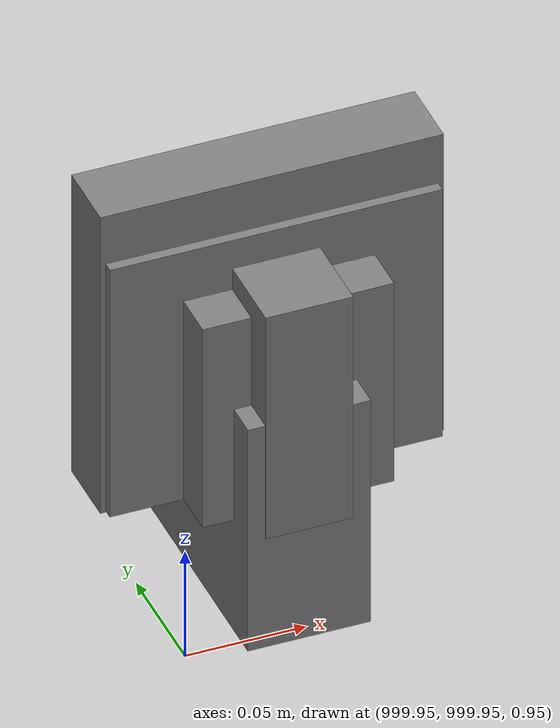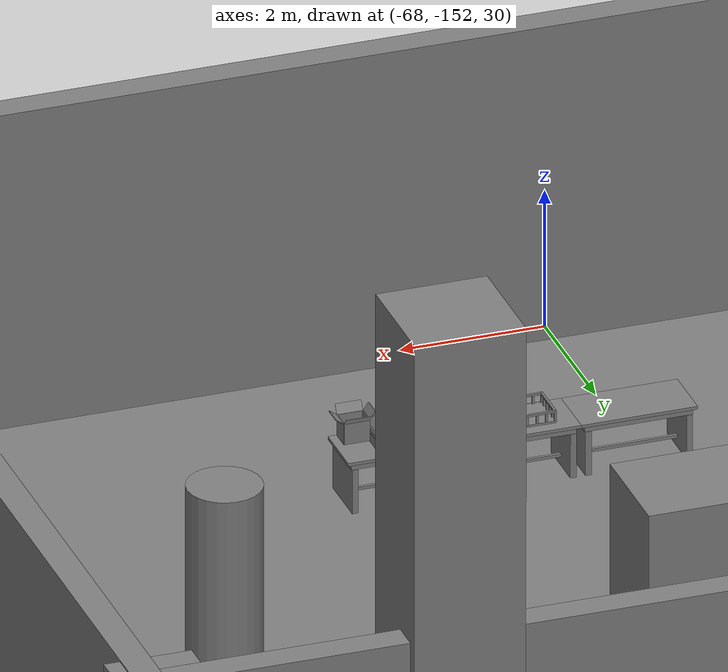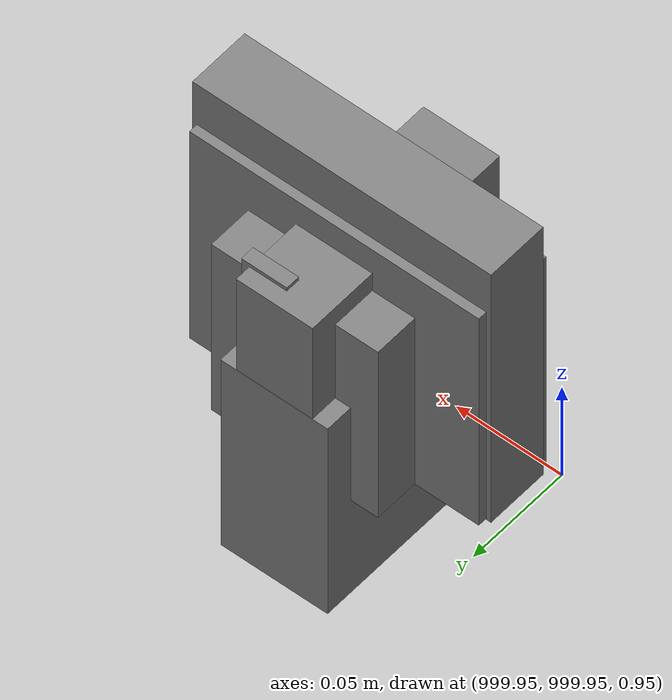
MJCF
<mujoco>
    <option gravity="0.000000000 0.000000000 -9.810000420" timestep="0.0049999999" integrator="implicitfast" density="1.225" viscosity="1.8000001e-05" noslip_iterations="10" iterations="100" sdf_iterations="50">
        <flag multiccd="disable"/>
    </option>
    <size memory="1000M"/>
    <compiler coordinate="local"/>
    <worldbody>
        <light cutoff="30" pos="0 1 1" dir="0 -1 -2"/>
        <light cutoff="30" pos="0 -1 1" dir="0 1 -2"/>
        <body pos="1000.000000000 1000.000000000 1.000000000" euler="0.000011953 0.000005123 -179.999984741" name="openloong_gripper_2f85_fix_base_usda_intel_box">
            <geom contype="1" conaffinity="1" density="1000" type="box" material="" rgba="0.500000000 0.500000000 0.500000000 1.000000000" solimp="0.899999976 0.949999988 0.001000000" friction="1.000000000 0.005000000 0.000100000" solref="0.020000000 1.000000000" margin="0" condim="3" group="0" pos="0.000000000 -0.000067139 0.000082284" quat="0.707106709 0.000000225 0.000000253 0.707106650" size="0.052800003 0.025300000 0.052800003" name="openloong_gripper_2f85_fix_base_usda_geom_B2847F4C_8999_4833_BBB0_FB8B5E25DA93"/>
            <freejoint name="openloong_gripper_2f85_fix_base_usda_intel_box_joint"/>
            <site size="0.005000000 0.005000000 0.005000000" rgba="0.500000000 0.500000000 0.500000000 1.000000000" pos="0.000000000 0.000000000 0.000000000" quat="0.999961913 0.008726500 0.000000000 0.000000000" group="0" type="sphere" name="openloong_gripper_2f85_fix_base_usda_intel_boxsite"/>
        </body>
        <body pos="1000.000000000 1000.000000000 1.000000000" euler="0.000000000 0.000000000 180.000000000" name="openloong_gripper_2f85_fix_base_usda_battery_01">
            <geom contype="1" conaffinity="1" density="1000" type="box" material="" rgba="0.500000000 0.500000000 0.500000000 1.000000000" solimp="0.899999976 0.949999988 0.001000000" friction="1.000000000 0.005000000 0.000100000" solref="0.020000000 1.000000000" margin="0" condim="3" group="0" pos="-0.011123657 -0.041940309 0.101691343" quat="1.000000000 0.000000000 0.000000000 0.000000000" size="0.010800000 0.003375000 0.004725000" name="openloong_gripper_2f85_fix_base_usda_geom_BE7B0713_F527_4180_B946_9114528D1AA8"/>
            <geom contype="1" conaffinity="1" density="1000" type="box" material="" rgba="0.500000000 0.500000000 0.500000000 1.000000000" solimp="0.899999976 0.949999988 0.001000000" friction="1.000000000 0.005000000 0.000100000" solref="0.020000000 1.000000000" margin="0" condim="3" group="0" pos="-0.010876465 -0.044247437 0.047066893" quat="0.998702705 -0.050920475 0.000000000 0.000000000" size="0.009450001 0.002700000 0.024975000" name="openloong_gripper_2f85_fix_base_usda_geom_EC344B18_4E5A_4DEC_BB04_C2F395F69041"/>
            <geom contype="1" conaffinity="1" density="1000" type="box" material="" rgba="0.500000000 0.500000000 0.500000000 1.000000000" solimp="0.899999976 0.949999988 0.001000000" friction="1.000000000 0.005000000 0.000100000" solref="0.020000000 1.000000000" margin="0" condim="3" group="0" pos="-0.001235962 -0.000659180 0.047381196" quat="1.000000000 0.000000000 0.000000000 0.000000000" size="0.039420001 0.039150000 0.047250003" name="openloong_gripper_2f85_fix_base_usda_geom_47352A53_9368_46E7_8889_C31533A348BC"/>
            <geom contype="1" conaffinity="1" density="1000" type="box" material="" rgba="0.500000000 0.500000000 0.500000000 1.000000000" solimp="0.899999976 0.949999988 0.001000000" friction="1.000000000 0.005000000 0.000100000" solref="0.020000000 1.000000000" margin="0" condim="3" group="0" pos="-0.010876465 -0.039138794 0.009851727" quat="1.000000000 0.000000000 0.000000000 0.000000000" size="0.009450001 0.010800000 0.013500000" name="openloong_gripper_2f85_fix_base_usda_geom_B6C789B2_8302_4E68_9895_8B8D5061B30C"/>
            <geom contype="1" conaffinity="1" density="1000" type="box" material="" rgba="0.500000000 0.500000000 0.500000000 1.000000000" solimp="0.899999976 0.949999988 0.001000000" friction="1.000000000 0.005000000 0.000100000" solref="0.020000000 1.000000000" margin="0" condim="3" group="0" pos="-0.010876465 -0.041528322 0.071508206" quat="1.000000000 0.000000000 0.000000000 0.000000000" size="0.009450001 0.002700000 0.027000001" name="openloong_gripper_2f85_fix_base_usda_geom_ACD99722_9132_43A5_88A7_F799E548EE35"/>
            <freejoint name="openloong_gripper_2f85_fix_base_usda_battery_01_joint"/>
            <site size="0.005000000 0.005000000 0.005000000" rgba="0.500000000 0.500000000 0.500000000 1.000000000" pos="0.000000000 0.000000000 0.000000000" quat="0.999961913 0.008726500 0.000000000 0.000000000" group="0" type="sphere" name="openloong_gripper_2f85_fix_base_usda_battery_01site"/>
        </body>
        <body pos="-65.890243530 -148.885803223 31.162685394" euler="33.241847992 -66.837638855 153.688781738" mocap="true" name="spotlight4_SpotLight"/>
        <body pos="1000.000000000 1000.000000000 1.000000000" euler="0.000000000 0.000000000 180.000000000" name="openloong_gripper_2f85_fix_base_usda_cpu_fan">
            <geom contype="1" conaffinity="1" density="1000" type="box" material="" rgba="0.500000000 0.500000000 0.500000000 1.000000000" solimp="0.899999976 0.949999988 0.001000000" friction="1.000000000 0.005000000 0.000100000" solref="0.020000000 1.000000000" margin="0" condim="3" group="0" pos="0.000000000 0.000000000 0.070034981" quat="0.000000000 0.000000000 0.000000000 1.000000000" size="0.070700005 0.014699999 0.070700005" name="openloong_gripper_2f85_fix_base_usda_geom_A76D0683_C911_474B_A238_AEEB864C6F6E"/>
            <freejoint name="openloong_gripper_2f85_fix_base_usda_cpu_fan_joint"/>
            <site size="0.005000000 0.005000000 0.005000000" rgba="0.500000000 0.500000000 0.500000000 1.000000000" pos="0.000000000 0.000000000 0.000000000" quat="0.999961913 0.008726535 0.000000000 0.000000000" group="0" type="sphere" name="openloong_gripper_2f85_fix_base_usda_cpu_fancsite"/>
        </body>
        <body pos="1000.000000000 1000.000000000 1.000000000" euler="0.000000000 0.000000000 180.000000000" name="openloong_gripper_2f85_fix_base_usda_wifi_box">
            <geom contype="1" conaffinity="1" density="1000" type="box" material="" rgba="0.500000000 0.500000000 0.500000000 1.000000000" solimp="0.899999976 0.949999988 0.001000000" friction="1.000000000 0.005000000 0.000100000" solref="0.020000000 1.000000000" margin="0" condim="3" group="0" pos="0.000000000 0.000000000 0.058978677" quat="0.000000000 0.000000047 0.000000000 1.000000000" size="0.068499997 0.018999999 0.059000000" name="openloong_gripper_2f85_fix_base_usda_geom_F0F94873_3B1D_4095_A359_320646DD2200"/>
            <freejoint name="openloong_gripper_2f85_fix_base_usda_wifi_box_joint"/>
            <site size="0.005000000 0.005000000 0.005000000" rgba="0.500000000 0.500000000 0.500000000 1.000000000" pos="0.000000000 0.000000000 0.000000000" quat="0.999961913 0.008726500 0.000000000 0.000000000" group="0" type="sphere" name="openloong_gripper_2f85_fix_base_usda_wifi_boxsite"/>
        </body>
        <body pos="-66.253456116 -149.633773804 31.162584305" euler="31.666210175 -64.638938904 110.611831665" mocap="true" name="spotlight5_SpotLight"/>
        <body pos="1000.000000000 999.999938965 1.000000000" euler="0.000000000 0.000000000 180.000000000" name="openloong_gripper_2f85_fix_base_usda_intelcore_i5">
            <geom contype="1" conaffinity="1" density="1000" type="box" material="" rgba="0.500000000 0.500000000 0.500000000 1.000000000" solimp="0.899999976 0.949999988 0.001000000" friction="1.000000000 0.005000000 0.000100000" solref="0.020000000 1.000000000" margin="0" condim="3" group="0" pos="0.000000000 0.000000000 0.051722717" quat="0.707106709 0.000000000 0.000000000 -0.707106769" size="0.052800000 0.018080002 0.052800000" name="openloong_gripper_2f85_fix_base_usda_geom_6BE4515C_847D_4656_A801_8698C5DA28C4"/>
            <freejoint name="openloong_gripper_2f85_fix_base_usda_intelcore_i5_joint"/>
            <site size="0.005000000 0.005000000 0.005000000" rgba="0.500000000 0.500000000 0.500000000 1.000000000" pos="0.000000000 0.000000000 0.000000000" quat="0.999961913 0.008726534 0.000000000 0.000000000" group="0" type="sphere" name="openloong_gripper_2f85_fix_base_usda_intelcore_i5site"/>
        </body>
        <body pos="-65.877098083 -149.709762573 31.171106339" euler="-24.689779282 19.791255951 -86.120384216" mocap="true" name="spotlight1_SpotLight"/>
        <body pos="-64.866622925 -149.383972168 30.183746338" euler="89.999984741 89.999946594 0.000000000" name="openloong_gripper_2f85_fix_base_usda_bluebox_01">
            <geom contype="1" conaffinity="1" density="1000" type="box" material="" rgba="0.500000000 0.500000000 0.500000000 1.000000000" solimp="0.899999976 0.949999988 0.001000000" friction="1.000000000 0.005000000 0.000100000" solref="0.020000000 1.000000000" margin="0" condim="3" group="0" pos="0.276580811 0.187225342 0.000068665" quat="0.707106948 0.000077471 0.707106352 0.000077486" size="0.100000001 0.057999998 0.010000000" name="openloong_gripper_2f85_fix_base_usda_geom_59D1B098_0150_4119_9739_8C935B3200DA"/>
            <geom contype="1" conaffinity="1" density="1000" type="box" material="" rgba="0.500000000 0.500000000 0.500000000 1.000000000" solimp="0.899999976 0.949999988 0.001000000" friction="1.000000000 0.005000000 0.000100000" solref="0.020000000 1.000000000" margin="0" condim="3" group="0" pos="0.000000000 0.002883911 0.000000000" quat="0.999999881 0.000000000 0.000000000 0.000000000" size="0.254000008 0.003000000 0.172000006" name="openloong_gripper_2f85_fix_base_usda_geom_313A455B_0E27_42A5_A2D1_DC49D2324721"/>
            <geom contype="1" conaffinity="1" density="1000" type="box" material="" rgba="0.500000000 0.500000000 0.500000000 1.000000000" solimp="0.899999976 0.949999988 0.001000000" friction="1.000000000 0.005000000 0.000100000" solref="0.020000000 1.000000000" margin="0" condim="3" group="0" pos="0.000000000 0.124874115 0.173484802" quat="0.999796331 0.020176515 -0.000000015 0.000000030" size="0.259999990 0.119999997 0.007000000" name="openloong_gripper_2f85_fix_base_usda_geom_18E03199_1A50_4993_885E_ACD97783FC51"/>
            <geom contype="1" conaffinity="1" density="1000" type="box" material="" rgba="0.500000000 0.500000000 0.500000000 1.000000000" solimp="0.899999976 0.949999988 0.001000000" friction="1.000000000 0.005000000 0.000100000" solref="0.020000000 1.000000000" margin="0" condim="3" group="0" pos="0.000000000 0.124874115 -0.173469543" quat="0.999796331 -0.020176545 -0.000000015 0.000000000" size="0.259999990 0.119999997 0.007000000" name="openloong_gripper_2f85_fix_base_usda_geom_E1FF88BF_E7BE_4F64_843C_98FB6C2CE602"/>
            <geom contype="1" conaffinity="1" density="1000" type="box" material="" rgba="0.500000000 0.500000000 0.500000000 1.000000000" solimp="0.899999976 0.949999988 0.001000000" friction="1.000000000 0.005000000 0.000100000" solref="0.020000000 1.000000000" margin="0" condim="3" group="0" pos="0.000000000 0.214008331 0.188980103" quat="0.999912977 0.013176724 0.000000015 0.000000000" size="0.259999990 0.029999999 0.012500000" name="openloong_gripper_2f85_fix_base_usda_geom_44087274_70F2_49FF_A9AC_32FB4847C2B8"/>
            <geom contype="1" conaffinity="1" density="1000" type="box" material="" rgba="0.500000000 0.500000000 0.500000000 1.000000000" solimp="0.899999976 0.949999988 0.001000000" friction="1.000000000 0.005000000 0.000100000" solref="0.020000000 1.000000000" margin="0" condim="3" group="0" pos="-0.258361816 0.125289917 0.001876831" quat="0.702796936 -0.020792112 0.710783124 0.020769298" size="0.189999998 0.119999997 0.009000000" name="openloong_gripper_2f85_fix_base_usda_geom_3E9FE3E1_BBC1_4A2C_BDD7_788F0D302485"/>
            <geom contype="1" conaffinity="1" density="1000" type="box" material="" rgba="0.500000000 0.500000000 0.500000000 1.000000000" solimp="0.899999976 0.949999988 0.001000000" friction="1.000000000 0.005000000 0.000100000" solref="0.020000000 1.000000000" margin="0" condim="3" group="0" pos="0.000000000 0.214008331 -0.188980103" quat="0.999912977 -0.013176769 0.000000030 0.000000015" size="0.259999990 0.029999999 0.012500000" name="openloong_gripper_2f85_fix_base_usda_geom_0B132543_5891_4474_9619_E3DF38BD91A7"/>
            <geom contype="1" conaffinity="1" density="1000" type="box" material="" rgba="0.500000000 0.500000000 0.500000000 1.000000000" solimp="0.899999976 0.949999988 0.001000000" friction="1.000000000 0.005000000 0.000100000" solref="0.020000000 1.000000000" margin="0" condim="3" group="0" pos="-0.276611328 0.187225342 0.000068665" quat="0.707106650 0.000077441 0.707106709 0.000077456" size="0.100000001 0.057999998 0.010000000" name="openloong_gripper_2f85_fix_base_usda_geom_2B584D8F_2069_4F9C_979F_AB925C7C2581"/>
            <geom contype="1" conaffinity="1" density="1000" type="box" material="" rgba="0.500000000 0.500000000 0.500000000 1.000000000" solimp="0.899999976 0.949999988 0.001000000" friction="1.000000000 0.005000000 0.000100000" solref="0.020000000 1.000000000" margin="0" condim="3" group="0" pos="0.258331299 0.125289917 0.001876831" quat="0.702851415 0.018856421 0.710823774 -0.019329369" size="0.189999998 0.119999997 0.009000000" name="openloong_gripper_2f85_fix_base_usda_geom_678A4C7F_235F_4948_AC76_BBE234337D07"/>
            <freejoint name="openloong_gripper_2f85_fix_base_usda_bluebox_01_joint"/>
            <site size="0.005000000 0.005000000 0.005000000" rgba="0.500000000 0.500000000 0.500000000 1.000000000" pos="0.000000000 0.000000000 0.000000000" quat="0.999961913 0.008726534 0.000000000 0.000000000" group="0" type="sphere" name="openloong_gripper_2f85_fix_base_usda_bluebox_01site"/>
        </body>
        <body pos="-64.496299744 -149.491867065 30.235729218" euler="0.000000000 0.000000000 89.999946594" name="openloong_gripper_2f85_fix_base_usda_cardboardbox_01">
            <geom contype="1" conaffinity="1" density="1000" type="box" material="" rgba="0.500000000 0.500000000 0.500000000 1.000000000" solimp="0.899999976 0.949999988 0.001000000" friction="1.000000000 0.005000000 0.000100000" solref="0.020000000 1.000000000" margin="0" condim="3" group="0" pos="-0.003166199 -0.004086494 0.005052090" quat="1.000000000 0.000000000 0.000000000 0.000000000" size="0.142499998 0.177500010 0.005000000" name="openloong_gripper_2f85_fix_base_usda_geom_FB8EC182_4992_401D_9947_C2F133280B42"/>
            <geom contype="1" conaffinity="1" density="1000" type="box" material="" rgba="0.500000000 0.500000000 0.500000000 1.000000000" solimp="0.899999976 0.949999988 0.001000000" friction="1.000000000 0.005000000 0.000100000" solref="0.020000000 1.000000000" margin="0" condim="3" group="0" pos="-0.003166199 0.170316696 0.150570869" quat="1.000000000 0.000000000 0.000000000 0.000000000" size="0.142499998 0.005000000 0.149999991" name="openloong_gripper_2f85_fix_base_usda_geom_BB39D284_0CAF_4EEC_BEE2_650D7C64EA6E"/>
            <geom contype="1" conaffinity="1" density="1000" type="box" material="" rgba="0.500000000 0.500000000 0.500000000 1.000000000" solimp="0.899999976 0.949999988 0.001000000" friction="1.000000000 0.005000000 0.000100000" solref="0.020000000 1.000000000" margin="0" condim="3" group="0" pos="-0.147399902 -0.005307198 0.150570869" quat="1.000000000 0.000000000 0.000000000 0.000000000" size="0.005000000 0.177500010 0.149999991" name="openloong_gripper_2f85_fix_base_usda_geom_7B25B4DE_74CD_44AB_9CCE_5F71C852476E"/>
            <geom contype="1" conaffinity="1" density="1000" type="box" material="" rgba="0.500000000 0.500000000 0.500000000 1.000000000" solimp="0.899999976 0.949999988 0.001000000" friction="1.000000000 0.005000000 0.000100000" solref="0.020000000 1.000000000" margin="0" condim="3" group="0" pos="0.140275955 -0.005307198 0.150570869" quat="1.000000000 0.000000000 0.000000000 0.000000000" size="0.005000000 0.177500010 0.149999991" name="openloong_gripper_2f85_fix_base_usda_geom_5A8081E0_CC4C_4DDE_943C_79A4E4DBB521"/>
            <geom contype="1" conaffinity="1" density="1000" type="box" material="" rgba="0.500000000 0.500000000 0.500000000 1.000000000" solimp="0.899999976 0.949999988 0.001000000" friction="1.000000000 0.005000000 0.000100000" solref="0.020000000 1.000000000" margin="0" condim="3" group="0" pos="-0.003166199 -0.181550980 0.150570869" quat="1.000000000 0.000000000 0.000000000 0.000000000" size="0.142499998 0.005000000 0.149999991" name="openloong_gripper_2f85_fix_base_usda_geom_BF2FCC21_7387_4F5A_8021_C5B2C4A0070B"/>
            <freejoint name="openloong_gripper_2f85_fix_base_usda_cardboardbox_01_joint"/>
            <site size="0.005000000 0.005000000 0.005000000" rgba="0.500000000 0.500000000 0.500000000 1.000000000" pos="0.000000000 0.000000000 0.000000000" quat="0.999961913 0.008726535 0.000000000 0.000000000" group="0" type="sphere" name="openloong_gripper_2f85_fix_base_usda_site_E227BDA3_A76B_4BD9_9FE6_32D05A683303"/>
            <body pos="0.139160156 -0.004048347 0.301930904" euler="-179.999954224 49.383502960 179.999954224" name="openloong_gripper_2f85_fix_base_usda_A1_006">
                <geom contype="1" conaffinity="1" density="1000" type="box" material="" rgba="0.500000000 0.500000000 0.500000000 1.000000000" solimp="0.899999976 0.949999988 0.001000000" friction="1.000000000 0.005000000 0.000100000" solref="0.020000000 1.000000000" margin="0" condim="3" group="0" pos="-0.071587563 0.000009537 0.001745224" quat="0.999999881 0.000000000 0.000000000 0.000000000" size="0.071249999 0.179999992 0.002500000" name="openloong_gripper_2f85_fix_base_usda_geom_82F38CD8_B4B1_4BAE_A301_6CE25D0A1541"/>
                <joint armature="0" stiffness="0.07" damping="0.0099999998" axis="0.000000 1.000000 0.000000" type="hinge" name="openloong_gripper_2f85_fix_base_usda_A1_006"/>
            </body>
            <body pos="-0.145902634 -0.004086494 0.301938057" euler="-180.000000000 -60.000011444 -180.000000000" name="openloong_gripper_2f85_fix_base_usda_A2_006">
                <geom contype="1" conaffinity="1" density="1000" type="box" material="" rgba="0.500000000 0.500000000 0.500000000 1.000000000" solimp="0.899999976 0.949999988 0.001000000" friction="1.000000000 0.005000000 0.000100000" solref="0.020000000 1.000000000" margin="0" condim="3" group="0" pos="0.071268082 0.000009537 0.002717972" quat="0.000002921 0.000000000 -0.000000030 0.999999881" size="0.071249999 0.179999992 0.002500000" name="openloong_gripper_2f85_fix_base_usda_geom_946D4616_94D9_44C5_95D0_1C92BD7AAF39"/>
                <joint armature="0" stiffness="0.07" damping="0.0099999998" axis="0.000000 1.000000 0.000000" type="hinge" name="openloong_gripper_2f85_fix_base_usda_A2_006"/>
            </body>
            <body pos="-0.003385544 0.175991058 0.301930904" euler="-125.858116150 -0.000004561 0.000002331" name="openloong_gripper_2f85_fix_base_usda_B2_006">
                <geom contype="1" conaffinity="1" density="1000" type="box" material="" rgba="0.500000000 0.500000000 0.500000000 1.000000000" solimp="0.899999976 0.949999988 0.001000000" friction="1.000000000 0.005000000 0.000100000" solref="0.020000000 1.000000000" margin="0" condim="3" group="0" pos="0.000009537 -0.070939064 -0.002470016" quat="0.999614120 0.027776197 -0.000000015 0.000000030" size="0.137500003 0.064999998 0.005000000" name="openloong_gripper_2f85_fix_base_usda_geom_1AC5BF8B_224A_4B88_BED2_4AC075E0665C"/>
                <joint armature="0" stiffness="0.07" damping="0.0099999998" axis="1.000000 0.000000 0.000000" type="hinge" name="openloong_gripper_2f85_fix_base_usda_B2_006"/>
            </body>
            <body pos="-0.003385544 -0.184140205 0.301938057" euler="147.805557251 0.000000000 0.000000000" name="openloong_gripper_2f85_fix_base_usda_B1_006">
                <geom contype="1" conaffinity="1" density="1000" type="box" material="" rgba="0.500000000 0.500000000 0.500000000 1.000000000" solimp="0.899999976 0.949999988 0.001000000" friction="1.000000000 0.005000000 0.000100000" solref="0.020000000 1.000000000" margin="0" condim="3" group="0" pos="-0.000028610 0.070202351 -0.002703667" quat="0.999614179 -0.027776167 0.000000000 0.000000000" size="0.137500003 0.064999998 0.005000000" name="openloong_gripper_2f85_fix_base_usda_geom_EE13332D_2759_4E52_A4BA_D44DF56FFE98"/>
                <joint armature="0" stiffness="0.07" damping="0.0099999998" axis="1.000000 0.000000 0.000000" type="hinge" name="openloong_gripper_2f85_fix_base_usda_B1_006"/>
            </body>
        </body>
        <body pos="-65.882858276 -149.481979370 30.229999542" euler="-64.487716675 0.000000000 0.000000000" name="openloong_gripper_2f85_fix_base_usda_Barcode">
            <geom contype="1" conaffinity="1" density="1000" type="box" material="" rgba="0.500000000 0.500000000 0.500000000 1.000000000" solimp="0.899999976 0.949999988 0.001000000" friction="1.000000000 0.005000000 0.000100000" solref="0.020000000 1.000000000" margin="0" condim="3" group="0" pos="0.000000000 0.013038635 0.001419067" quat="0.000000000 0.000000000 0.000000000 1.000000119" size="0.034000002 0.010000000 0.017999999" name="openloong_gripper_2f85_fix_base_usda_geom_9B920D9E_6568_4B66_A164_88F0CE6495CD"/>
            <geom contype="1" conaffinity="1" density="1000" type="box" material="" rgba="0.500000000 0.500000000 0.500000000 1.000000000" solimp="0.899999976 0.949999988 0.001000000" friction="1.000000000 0.005000000 0.000100000" solref="0.020000000 1.000000000" margin="0" condim="3" group="0" pos="0.000000000 -0.035301208 -0.007095337" quat="0.000000000 0.000000000 -0.043619365 0.999048233" size="0.028999999 0.010000000 0.020000000" name="openloong_gripper_2f85_fix_base_usda_geom_84DFD584_47C8_4A4C_815D_2A941E38F0CA"/>
            <geom contype="1" conaffinity="1" density="1000" type="box" material="" rgba="0.500000000 0.500000000 0.500000000 1.000000000" solimp="0.899999976 0.949999988 0.001000000" friction="1.000000000 0.005000000 0.000100000" solref="0.020000000 1.000000000" margin="0" condim="3" group="0" pos="0.000000000 -0.043411255 -0.011749268" quat="0.922262907 0.386563420 0.000000000 0.000000000" size="0.026000001 0.010000000 0.020000000" name="openloong_gripper_2f85_fix_base_usda_geom_9F06490E_0597_49F6_9BDE_11E3B9C11F5C"/>
            <geom contype="1" conaffinity="1" density="1000" type="box" material="" rgba="0.500000000 0.500000000 0.500000000 1.000000000" solimp="0.899999976 0.949999988 0.001000000" friction="1.000000000 0.005000000 0.000100000" solref="0.020000000 1.000000000" margin="0" condim="3" group="0" pos="0.000000000 -0.016967773 -0.031860352" quat="0.000000000 0.000000000 0.000000000 1.000000119" size="0.008000000 0.010000000 0.013000000" name="openloong_gripper_2f85_fix_base_usda_geom_88769281_DE4A_45DA_87A5_5A0993E15795"/>
            <geom contype="1" conaffinity="1" density="1000" type="box" material="" rgba="0.500000000 0.500000000 0.500000000 1.000000000" solimp="0.899999976 0.949999988 0.001000000" friction="1.000000000 0.005000000 0.000100000" solref="0.020000000 1.000000000" margin="0" condim="3" group="0" pos="0.000000000 -0.001869202 0.000312805" quat="0.953716993 0.300705761 0.000000000 0.000000000" size="0.032000002 0.010000000 0.018999999" name="openloong_gripper_2f85_fix_base_usda_geom_699E35E7_0D44_4931_AFF2_8AB4BEC9BD6D"/>
            <geom contype="1" conaffinity="1" density="1000" type="box" material="" rgba="0.500000000 0.500000000 0.500000000 1.000000000" solimp="0.899999976 0.949999988 0.001000000" friction="1.000000000 0.005000000 0.000100000" solref="0.020000000 1.000000000" margin="0" condim="3" group="0" pos="0.000000000 -0.019531250 -0.003173828" quat="0.953716993 0.300705761 0.000000000 0.000000000" size="0.030999999 0.010000000 0.020000000" name="openloong_gripper_2f85_fix_base_usda_geom_DB427B6A_A34F_4688_90B8_D950F53A0251"/>
            <geom contype="1" conaffinity="1" density="1000" type="box" material="" rgba="0.500000000 0.500000000 0.500000000 1.000000000" solimp="0.899999976 0.949999988 0.001000000" friction="1.000000000 0.005000000 0.000100000" solref="0.020000000 1.000000000" margin="0" condim="3" group="0" pos="0.000000000 -0.035301208 -0.007095337" quat="0.953716993 0.300705761 0.000000000 0.000000000" size="0.028999999 0.010000000 0.020000000" name="openloong_gripper_2f85_fix_base_usda_geom_CF9B08DB_CF8A_419A_9971_345373A57BEF"/>
            <geom contype="1" conaffinity="1" density="1000" type="box" material="" rgba="0.500000000 0.500000000 0.500000000 1.000000000" solimp="0.899999976 0.949999988 0.001000000" friction="1.000000000 0.005000000 0.000100000" solref="0.020000000 1.000000000" margin="0" condim="3" group="0" pos="0.000000000 -0.042617798 -0.071121216" quat="0.000000000 0.000000000 0.000000000 1.000000119" size="0.013000000 0.021000000 0.059999999" name="openloong_gripper_2f85_fix_base_usda_geom_788A0AF8_BB41_4FB9_9787_22576DB00F21"/>
            <freejoint name="openloong_gripper_2f85_fix_base_usda_Barcode_joint"/>
            <site size="0.005000000 0.005000000 0.005000000" rgba="0.500000000 0.500000000 0.500000000 1.000000000" pos="0.000000000 0.000000000 0.000000000" quat="1.000000000 0.000000000 0.000000000 0.000000000" group="0" type="sphere" name="openloong_gripper_2f85_fix_base_usda_Barcode_site"/>
        </body>
        <body pos="-66.745018005 -149.392349243 30.184000015" euler="0.000000000 0.000000000 89.999946594" name="[22333510399408]_Basket_01">
            <geom contype="1" conaffinity="1" density="1000" type="box" material="" rgba="0.500000000 0.500000000 0.500000000 1.000000000" solimp="0.899999976 0.949999988 0.001000000" friction="1.000000000 0.005000000 0.000100000" solref="0.020000000 1.000000000" margin="0" condim="3" group="0" pos="-0.052425385 0.389207840 0.089787483" quat="0.707107008 0.000000000 0.000000000 0.707106411" size="0.014249999 0.014249999 0.059999999" name="[22333510399408]_geom_CE84BD1A_D734_4A88_84D7_0B2DF38DAA83"/>
            <geom contype="1" conaffinity="1" density="1000" type="box" material="" rgba="0.500000000 0.500000000 0.500000000 1.000000000" solimp="0.899999976 0.949999988 0.001000000" friction="1.000000000 0.005000000 0.000100000" solref="0.020000000 1.000000000" margin="0" condim="3" group="0" pos="0.264015198 -0.133043289 0.089787483" quat="0.707107008 0.000000000 0.000000000 0.707106411" size="0.014249999 0.014249999 0.059999999" name="[22333510399408]_geom_247F5E9E_60A6_4E14_90E7_58048CEE4087"/>
            <geom contype="1" conaffinity="1" density="1000" type="box" material="" rgba="0.500000000 0.500000000 0.500000000 1.000000000" solimp="0.899999976 0.949999988 0.001000000" friction="1.000000000 0.005000000 0.000100000" solref="0.020000000 1.000000000" margin="0" condim="3" group="0" pos="-0.264015198 -0.265548706 0.089793205" quat="0.707107008 0.000000000 0.000000000 0.707106411" size="0.014249999 0.014249999 0.059999999" name="[22333510399408]_geom_D78693CD_FBA7_4CBA_ABC3_949BB576601B"/>
            <geom contype="1" conaffinity="1" density="1000" type="box" material="" rgba="0.500000000 0.500000000 0.500000000 1.000000000" solimp="0.899999976 0.949999988 0.001000000" friction="1.000000000 0.005000000 0.000100000" solref="0.020000000 1.000000000" margin="0" condim="3" group="0" pos="-0.160263062 -0.389322281 0.089793205" quat="0.707107008 0.000000000 0.000000000 0.707106411" size="0.014249999 0.014249999 0.059999999" name="[22333510399408]_geom_AAAD08D7_EC7A_49B7_AE4F_85F567C8E0AB"/>
            <geom contype="1" conaffinity="1" density="1000" type="box" material="" rgba="0.500000000 0.500000000 0.500000000 1.000000000" solimp="0.899999976 0.949999988 0.001000000" friction="1.000000000 0.005000000 0.000100000" solref="0.020000000 1.000000000" margin="0" condim="3" group="0" pos="0.162265778 -0.389322281 0.089787483" quat="0.707107008 0.000000000 0.000000000 0.707106411" size="0.014249999 0.014249999 0.059999999" name="[22333510399408]_geom_F469645D_3505_46D5_81D1_9F81157ED7E2"/>
            <geom contype="1" conaffinity="1" density="1000" type="box" material="" rgba="0.500000000 0.500000000 0.500000000 1.000000000" solimp="0.899999976 0.949999988 0.001000000" friction="1.000000000 0.005000000 0.000100000" solref="0.020000000 1.000000000" margin="0" condim="3" group="0" pos="0.264015198 0.389207840 0.089787483" quat="0.707107008 0.000000000 0.000000000 0.707106411" size="0.014249999 0.014249999 0.059999999" name="[22333510399408]_geom_E4EF4A29_F341_41A9_BA95_A1A863C59210"/>
            <geom contype="1" conaffinity="1" density="1000" type="box" material="" rgba="0.500000000 0.500000000 0.500000000 1.000000000" solimp="0.899999976 0.949999988 0.001000000" friction="1.000000000 0.005000000 0.000100000" solref="0.020000000 1.000000000" margin="0" condim="3" group="0" pos="-0.264015198 -0.133043289 0.089793205" quat="0.707107008 0.000000000 0.000000000 0.707106411" size="0.014249999 0.014249999 0.059999999" name="[22333510399408]_geom_A88813D6_1A0E_4CEB_8BC1_0E87874256C6"/>
            <geom contype="1" conaffinity="1" density="1000" type="box" material="" rgba="0.500000000 0.500000000 0.500000000 1.000000000" solimp="0.899999976 0.949999988 0.001000000" friction="1.000000000 0.005000000 0.000100000" solref="0.020000000 1.000000000" margin="0" condim="3" group="0" pos="-0.264026642 0.269256592 0.089793205" quat="0.707107008 0.000000000 0.000000000 0.707106411" size="0.014249999 0.014249999 0.059999999" name="[22333510399408]_geom_79DDE04E_373B_45F7_91F8_F272172FDDCA"/>
            <geom contype="1" conaffinity="1" density="1000" type="box" material="" rgba="0.500000000 0.500000000 0.500000000 1.000000000" solimp="0.899999976 0.949999988 0.001000000" friction="1.000000000 0.005000000 0.000100000" solref="0.020000000 1.000000000" margin="0" condim="3" group="0" pos="0.054462433 0.389207840 0.089787483" quat="0.707107008 0.000000000 0.000000000 0.707106411" size="0.014249999 0.014249999 0.059999999" name="[22333510399408]_geom_F6EBB9FA_69BC_44C6_AF48_212A3B314EF2"/>
            <geom contype="1" conaffinity="1" density="1000" type="box" material="" rgba="0.500000000 0.500000000 0.500000000 1.000000000" solimp="0.899999976 0.949999988 0.001000000" friction="1.000000000 0.005000000 0.000100000" solref="0.020000000 1.000000000" margin="0" condim="3" group="0" pos="0.054462433 -0.389322281 0.089787483" quat="0.707107008 0.000000000 0.000000000 0.707106411" size="0.014249999 0.014249999 0.059999999" name="[22333510399408]_geom_74EF2D94_6F7B_4D5D_9B1C_59B5F05DEEF9"/>
            <geom contype="1" conaffinity="1" density="1000" type="box" material="" rgba="0.500000000 0.500000000 0.500000000 1.000000000" solimp="0.899999976 0.949999988 0.001000000" friction="1.000000000 0.005000000 0.000100000" solref="0.020000000 1.000000000" margin="0" condim="3" group="0" pos="0.264015198 0.269256592 0.089793205" quat="0.707107008 0.000000000 0.000000000 0.707106411" size="0.014249999 0.014249999 0.059999999" name="[22333510399408]_geom_CEAE1A09_6BFC_4CD8_B8DD_D12FECB9CDF7"/>
            <geom contype="1" conaffinity="1" density="1000" type="box" material="" rgba="0.500000000 0.500000000 0.500000000 1.000000000" solimp="0.899999976 0.949999988 0.001000000" friction="1.000000000 0.005000000 0.000100000" solref="0.020000000 1.000000000" margin="0" condim="3" group="0" pos="0.264015198 -0.389322281 0.089787483" quat="0.707107008 0.000000000 0.000000000 0.707106411" size="0.014249999 0.014249999 0.059999999" name="[22333510399408]_geom_B6608A79_60A0_4CF9_9904_3446AF31D7D9"/>
            <geom contype="1" conaffinity="1" density="1000" type="box" material="" rgba="0.500000000 0.500000000 0.500000000 1.000000000" solimp="0.899999976 0.949999988 0.001000000" friction="1.000000000 0.005000000 0.000100000" solref="0.020000000 1.000000000" margin="0" condim="3" group="0" pos="0.000000000 0.000000000 0.015998840" quat="0.707107008 0.000000000 0.000000000 0.707106411" size="0.403499991 0.279000014 0.015750000" name="[22333510399408]_geom_3C03D2CB_8BA9_49C5_9F63_B250119F64AA"/>
            <geom contype="1" conaffinity="1" density="1000" type="box" material="" rgba="0.500000000 0.500000000 0.500000000 1.000000000" solimp="0.899999976 0.949999988 0.001000000" friction="1.000000000 0.005000000 0.000100000" solref="0.020000000 1.000000000" margin="0" condim="3" group="0" pos="0.000000000 -0.389476776 0.163619041" quat="0.707107008 0.000000000 0.000000000 0.707106411" size="0.015000000 0.277500004 0.015750000" name="[22333510399408]_geom_2E834167_ED66_40AC_AF56_A8D119C2A066"/>
            <geom contype="1" conaffinity="1" density="1000" type="box" material="" rgba="0.500000000 0.500000000 0.500000000 1.000000000" solimp="0.899999976 0.949999988 0.001000000" friction="1.000000000 0.005000000 0.000100000" solref="0.020000000 1.000000000" margin="0" condim="3" group="0" pos="0.162265778 0.389207840 0.089787483" quat="0.707107008 0.000000000 0.000000000 0.707106411" size="0.014249999 0.014249999 0.059999999" name="[22333510399408]_geom_7B54C62B_FC53_4F7E_8614_528CD67F08A5"/>
            <geom contype="1" conaffinity="1" density="1000" type="box" material="" rgba="0.500000000 0.500000000 0.500000000 1.000000000" solimp="0.899999976 0.949999988 0.001000000" friction="1.000000000 0.005000000 0.000100000" solref="0.020000000 1.000000000" margin="0" condim="3" group="0" pos="0.000000000 0.389471054 0.163619041" quat="0.707107008 0.000000000 0.000000000 0.707106411" size="0.015000000 0.277500004 0.015750000" name="[22333510399408]_geom_9F2902A9_0AC6_41BD_BF88_9AF84EBB8F0D"/>
            <geom contype="1" conaffinity="1" density="1000" type="box" material="" rgba="0.500000000 0.500000000 0.500000000 1.000000000" solimp="0.899999976 0.949999988 0.001000000" friction="1.000000000 0.005000000 0.000100000" solref="0.020000000 1.000000000" margin="0" condim="3" group="0" pos="-0.263511658 0.000000000 0.163619041" quat="0.707107008 0.000000000 0.000000000 0.707106411" size="0.403499991 0.015000000 0.015750000" name="[22333510399408]_geom_314DDAEC_3E6B_420C_A342_8E3686940FEB"/>
            <geom contype="1" conaffinity="1" density="1000" type="box" material="" rgba="0.500000000 0.500000000 0.500000000 1.000000000" solimp="0.899999976 0.949999988 0.001000000" friction="1.000000000 0.005000000 0.000100000" solref="0.020000000 1.000000000" margin="0" condim="3" group="0" pos="-0.264015198 0.141334534 0.089793205" quat="0.707107008 0.000000000 0.000000000 0.707106411" size="0.014249999 0.014249999 0.059999999" name="[22333510399408]_geom_4B4FE066_7F24_4D11_BD5A_1E3841EA73CE"/>
            <geom contype="1" conaffinity="1" density="1000" type="box" material="" rgba="0.500000000 0.500000000 0.500000000 1.000000000" solimp="0.899999976 0.949999988 0.001000000" friction="1.000000000 0.005000000 0.000100000" solref="0.020000000 1.000000000" margin="0" condim="3" group="0" pos="0.264015198 -0.265548706 0.089787483" quat="0.707107008 0.000000000 0.000000000 0.707106411" size="0.014249999 0.014249999 0.059999999" name="[22333510399408]_geom_61F2C2D9_189A_4C24_9394_7C4CA08E23F4"/>
            <geom contype="1" conaffinity="1" density="1000" type="box" material="" rgba="0.500000000 0.500000000 0.500000000 1.000000000" solimp="0.899999976 0.949999988 0.001000000" friction="1.000000000 0.005000000 0.000100000" solref="0.020000000 1.000000000" margin="0" condim="3" group="0" pos="-0.160263062 0.389207840 0.089787483" quat="0.707107008 0.000000000 0.000000000 0.707106411" size="0.014249999 0.014249999 0.059999999" name="[22333510399408]_geom_EA11567A_B90F_4C4C_8657_25ED06B8EA5E"/>
            <geom contype="1" conaffinity="1" density="1000" type="box" material="" rgba="0.500000000 0.500000000 0.500000000 1.000000000" solimp="0.899999976 0.949999988 0.001000000" friction="1.000000000 0.005000000 0.000100000" solref="0.020000000 1.000000000" margin="0" condim="3" group="0" pos="-0.052425385 -0.389322281 0.089787483" quat="0.707107008 0.000000000 0.000000000 0.707106411" size="0.014249999 0.014249999 0.059999999" name="[22333510399408]_geom_C59A20FF_8285_4110_B80E_9E7B88D88CDE"/>
            <geom contype="1" conaffinity="1" density="1000" type="box" material="" rgba="0.500000000 0.500000000 0.500000000 1.000000000" solimp="0.899999976 0.949999988 0.001000000" friction="1.000000000 0.005000000 0.000100000" solref="0.020000000 1.000000000" margin="0" condim="3" group="0" pos="-0.264026642 -0.389322281 0.089793205" quat="0.707107008 0.000000000 0.000000000 0.707106411" size="0.014249999 0.014249999 0.059999999" name="[22333510399408]_geom_9B6C46C4_D4B5_493F_8AFF_E28C88126E11"/>
            <geom contype="1" conaffinity="1" density="1000" type="box" material="" rgba="0.500000000 0.500000000 0.500000000 1.000000000" solimp="0.899999976 0.949999988 0.001000000" friction="1.000000000 0.005000000 0.000100000" solref="0.020000000 1.000000000" margin="0" condim="3" group="0" pos="0.264015198 0.141334534 0.089787483" quat="0.707107008 0.000000000 0.000000000 0.707106411" size="0.014249999 0.014249999 0.059999999" name="[22333510399408]_geom_D6463918_91E7_42AF_AE4A_F0CA95160CA0"/>
            <geom contype="1" conaffinity="1" density="1000" type="box" material="" rgba="0.500000000 0.500000000 0.500000000 1.000000000" solimp="0.899999976 0.949999988 0.001000000" friction="1.000000000 0.005000000 0.000100000" solref="0.020000000 1.000000000" margin="0" condim="3" group="0" pos="-0.264015198 0.389207840 0.089793205" quat="0.707107008 0.000000000 0.000000000 0.707106411" size="0.014249999 0.014249999 0.059999999" name="[22333510399408]_geom_81013228_51E1_4DD2_AF7C_18C5226F6E71"/>
            <geom contype="1" conaffinity="1" density="1000" type="box" material="" rgba="0.500000000 0.500000000 0.500000000 1.000000000" solimp="0.899999976 0.949999988 0.001000000" friction="1.000000000 0.005000000 0.000100000" solref="0.020000000 1.000000000" margin="0" condim="3" group="0" pos="0.264015198 0.004480362 0.089787483" quat="0.707107008 0.000000000 0.000000000 0.707106411" size="0.014249999 0.014249999 0.059999999" name="[22333510399408]_geom_D31ABC82_7B49_4628_B23A_31748F5E9253"/>
            <geom contype="1" conaffinity="1" density="1000" type="box" material="" rgba="0.500000000 0.500000000 0.500000000 1.000000000" solimp="0.899999976 0.949999988 0.001000000" friction="1.000000000 0.005000000 0.000100000" solref="0.020000000 1.000000000" margin="0" condim="3" group="0" pos="0.263694763 -0.000011444 0.163619041" quat="0.707107008 0.000000000 0.000000000 0.707106411" size="0.403499991 0.015000000 0.015750000" name="[22333510399408]_geom_92895AC2_1624_491D_8083_BE73161E04EF"/>
            <geom contype="1" conaffinity="1" density="1000" type="box" material="" rgba="0.500000000 0.500000000 0.500000000 1.000000000" solimp="0.899999976 0.949999988 0.001000000" friction="1.000000000 0.005000000 0.000100000" solref="0.020000000 1.000000000" margin="0" condim="3" group="0" pos="-0.264015198 0.004480362 0.089793205" quat="0.707107008 0.000000000 0.000000000 0.707106411" size="0.014249999 0.014249999 0.059999999" name="[22333510399408]_geom_DD08D58E_0582_4A51_89DE_4630F1504A74"/>
            <freejoint name="[22333510399408]_joint_E7C35EB6_6388_4011_B7ED_065DBD978705"/>
        </body>
        <body pos="0.000000000 0.000000000 0.000000000" euler="0.000000000 0.000000000 0.000000000" name="Static Objects_Static Objects">
            <geom contype="1" conaffinity="1" density="1000" type="box" material="" rgba="0.500000000 0.500000000 0.500000000 1.000000000" solimp="0.899999976 0.949999988 0.001000000" friction="1.000000000 0.005000000 0.000100000" solref="0.020000000 1.000000000" margin="0" condim="3" group="0" pos="-67.544113159 -149.365814209 29.727830887" quat="0.500000417 0.499999970 0.499999553 0.499999970" size="0.381000012 0.319999993 0.041000001" name="Static Objects_geom_6E18C316_81D7_4F51_AEA6_E8C179ADFD4F"/>
            <geom contype="1" conaffinity="1" density="1000" type="box" material="" rgba="0.500000000 0.500000000 0.500000000 1.000000000" solimp="0.899999976 0.949999988 0.001000000" friction="1.000000000 0.005000000 0.000100000" solref="0.020000000 1.000000000" margin="0" condim="3" group="0" pos="-68.239501953 -149.365814209 30.086868286" quat="0.500000417 0.499999970 0.499999553 0.499999970" size="0.370999992 0.039500002 0.745000005" name="Static Objects_geom_67328006_94A8_4480_8BB3_7B0A96507422"/>
            <geom contype="1" conaffinity="1" density="1000" type="box" material="" rgba="0.500000000 0.500000000 0.500000000 1.000000000" solimp="0.899999976 0.949999988 0.001000000" friction="1.000000000 0.005000000 0.000100000" solref="0.020000000 1.000000000" margin="0" condim="3" group="0" pos="-68.239501953 -149.365814209 30.147235870" quat="0.500000417 0.499999970 0.499999553 0.499999970" size="0.400000006 0.022000000 0.800000012" name="Static Objects_geom_C2B12DB0_09D8_4A98_A075_9DBBB1519B73"/>
            <geom contype="1" conaffinity="1" density="1000" type="box" material="" rgba="0.500000000 0.500000000 0.500000000 1.000000000" solimp="0.899999976 0.949999988 0.001000000" friction="1.000000000 0.005000000 0.000100000" solref="0.020000000 1.000000000" margin="0" condim="3" group="0" pos="-68.934890747 -149.365814209 29.727830887" quat="0.500000417 0.499999970 0.499999553 0.499999970" size="0.381000012 0.319999993 0.041000001" name="Static Objects_geom_1D03C7FD_4BB5_4666_A632_DA679B492A6F"/>
            <geom contype="1" conaffinity="1" density="1000" type="box" material="" rgba="0.500000000 0.500000000 0.500000000 1.000000000" solimp="0.899999976 0.949999988 0.001000000" friction="1.000000000 0.005000000 0.000100000" solref="0.020000000 1.000000000" margin="0" condim="3" group="0" pos="-68.239501953 -149.365814209 29.561563492" quat="0.500000417 0.499999970 0.499999553 0.499999970" size="0.020000000 0.022000000 0.660000026" name="Static Objects_geom_7991E7C7_F5A7_4259_9EBC_163680906E55"/>
            <geom contype="1" conaffinity="1" density="1000" type="box" material="" rgba="0.500000000 0.500000000 0.500000000 1.000000000" solimp="0.899999976 0.949999988 0.001000000" friction="1.000000000 0.005000000 0.000100000" solref="0.020000000 1.000000000" margin="0" condim="3" group="0" pos="-65.945671082 -149.365814209 29.727830887" quat="0.500000417 0.499999970 0.499999553 0.499999970" size="0.381000012 0.319999993 0.041000001" name="Static Objects_geom_A7E1A771_1F06_485B_865F_299D3ED409F5"/>
            <geom contype="1" conaffinity="1" density="1000" type="box" material="" rgba="0.500000000 0.500000000 0.500000000 1.000000000" solimp="0.899999976 0.949999988 0.001000000" friction="1.000000000 0.005000000 0.000100000" solref="0.020000000 1.000000000" margin="0" condim="3" group="0" pos="-66.641059875 -149.365814209 30.086868286" quat="0.500000417 0.499999970 0.499999553 0.499999970" size="0.370999992 0.039500002 0.745000005" name="Static Objects_geom_AA10D479_283C_4AA1_A8EF_5ACD644E9259"/>
            <geom contype="1" conaffinity="1" density="1000" type="box" material="" rgba="0.500000000 0.500000000 0.500000000 1.000000000" solimp="0.899999976 0.949999988 0.001000000" friction="1.000000000 0.005000000 0.000100000" solref="0.020000000 1.000000000" margin="0" condim="3" group="0" pos="-66.641059875 -149.365814209 30.147235870" quat="0.500000417 0.499999970 0.499999553 0.499999970" size="0.400000006 0.022000000 0.800000012" name="Static Objects_geom_7C7E0A10_6451_4E7F_9512_1F37CBCF96A2"/>
            <geom contype="1" conaffinity="1" density="1000" type="box" material="" rgba="0.500000000 0.500000000 0.500000000 1.000000000" solimp="0.899999976 0.949999988 0.001000000" friction="1.000000000 0.005000000 0.000100000" solref="0.020000000 1.000000000" margin="0" condim="3" group="0" pos="-67.336448669 -149.365814209 29.727830887" quat="0.500000417 0.499999970 0.499999553 0.499999970" size="0.381000012 0.319999993 0.041000001" name="Static Objects_geom_4B942FB9_9DA5_48F4_B4E3_54DCBE260D75"/>
            <geom contype="1" conaffinity="1" density="1000" type="box" material="" rgba="0.500000000 0.500000000 0.500000000 1.000000000" solimp="0.899999976 0.949999988 0.001000000" friction="1.000000000 0.005000000 0.000100000" solref="0.020000000 1.000000000" margin="0" condim="3" group="0" pos="-66.641059875 -149.365814209 29.561563492" quat="0.500000417 0.499999970 0.499999553 0.499999970" size="0.020000000 0.022000000 0.660000026" name="Static Objects_geom_A9A9FDFE_C4C1_4A3A_A67F_9C80E9DFF144"/>
            <geom contype="1" conaffinity="1" density="1000" type="box" material="" rgba="0.500000000 0.500000000 0.500000000 1.000000000" solimp="0.899999976 0.949999988 0.001000000" friction="1.000000000 0.005000000 0.000100000" solref="0.020000000 1.000000000" margin="0" condim="3" group="0" pos="-64.338577271 -149.365814209 29.727830887" quat="0.500000417 0.499999970 0.499999553 0.499999970" size="0.381000012 0.319999993 0.041000001" name="Static Objects_geom_97BECF80_A007_4E18_AFFB_F84FDC6D12CD"/>
            <geom contype="1" conaffinity="1" density="1000" type="box" material="" rgba="0.500000000 0.500000000 0.500000000 1.000000000" solimp="0.899999976 0.949999988 0.001000000" friction="1.000000000 0.005000000 0.000100000" solref="0.020000000 1.000000000" margin="0" condim="3" group="0" pos="-65.033966064 -149.365814209 30.086868286" quat="0.500000417 0.499999970 0.499999553 0.499999970" size="0.370999992 0.039500002 0.745000005" name="Static Objects_geom_51BCC754_8356_4D2D_B2F1_1553AC3AF56E"/>
            <geom contype="1" conaffinity="1" density="1000" type="box" material="" rgba="0.500000000 0.500000000 0.500000000 1.000000000" solimp="0.899999976 0.949999988 0.001000000" friction="1.000000000 0.005000000 0.000100000" solref="0.020000000 1.000000000" margin="0" condim="3" group="0" pos="-65.033966064 -149.365814209 30.147235870" quat="0.500000417 0.499999970 0.499999553 0.499999970" size="0.400000006 0.022000000 0.800000012" name="Static Objects_geom_7DA3EB94_032D_49E0_83C4_1EDD71CC57FB"/>
            <geom contype="1" conaffinity="1" density="1000" type="box" material="" rgba="0.500000000 0.500000000 0.500000000 1.000000000" solimp="0.899999976 0.949999988 0.001000000" friction="1.000000000 0.005000000 0.000100000" solref="0.020000000 1.000000000" margin="0" condim="3" group="0" pos="-65.729354858 -149.365814209 29.727830887" quat="0.500000417 0.499999970 0.499999553 0.499999970" size="0.381000012 0.319999993 0.041000001" name="Static Objects_geom_B2323195_88B1_4223_9557_71E920421324"/>
            <geom contype="1" conaffinity="1" density="1000" type="box" material="" rgba="0.500000000 0.500000000 0.500000000 1.000000000" solimp="0.899999976 0.949999988 0.001000000" friction="1.000000000 0.005000000 0.000100000" solref="0.020000000 1.000000000" margin="0" condim="3" group="0" pos="-65.033966064 -149.365814209 29.561563492" quat="0.500000417 0.499999970 0.499999553 0.499999970" size="0.020000000 0.022000000 0.660000026" name="Static Objects_geom_D8E454F1_5CA1_47F7_9022_A15F7498CA4E"/>
            <geom contype="1" conaffinity="1" density="1000" type="box" material="" rgba="0.500000000 0.500000000 0.500000000 1.000000000" solimp="0.899999976 0.949999988 0.001000000" friction="1.000000000 0.005000000 0.000100000" solref="0.020000000 1.000000000" margin="0" condim="3" group="0" pos="-61.754566193 -137.853729248 33.906845093" quat="0.707107067 0.000000000 0.000000000 0.707106471" size="0.759999990 0.759999990 4.500000000" name="Static Objects_geom_DCA81CE0_4D50_4425_9C37_0D0F05546D4D"/>
            <geom contype="1" conaffinity="1" density="1000" type="box" material="" rgba="0.500000000 0.500000000 0.500000000 1.000000000" solimp="0.899999976 0.949999988 0.001000000" friction="1.000000000 0.005000000 0.000100000" solref="0.020000000 1.000000000" margin="0" condim="3" group="0" pos="-57.511135101 -144.927108765 31.707921982" quat="1.000000000 0.000000000 0.000000000 0.000000000" size="0.200000003 8.000000000 2.299999952" name="Static Objects_geom_4EC8B332_E659_4719_A8F5_FFD428089552"/>
            <geom contype="1" conaffinity="1" density="1000" type="box" material="" rgba="0.500000000 0.500000000 0.500000000 1.000000000" solimp="0.899999976 0.949999988 0.001000000" friction="1.000000000 0.005000000 0.000100000" solref="0.020000000 1.000000000" margin="0" condim="3" group="0" pos="-80.517646790 -157.574050903 31.688196182" quat="0.707107067 0.000000000 0.000000000 0.707106471" size="0.600000024 0.600000024 2.299999952" name="Static Objects_geom_2172F9E3_4BEC_41FC_9696_0319CE32A7D8"/>
            <geom contype="1" conaffinity="1" density="1000" type="box" material="" rgba="0.500000000 0.500000000 0.500000000 1.000000000" solimp="0.899999976 0.949999988 0.001000000" friction="1.000000000 0.005000000 0.000100000" solref="0.020000000 1.000000000" margin="0" condim="3" group="0" pos="-80.711044312 -147.414932251 31.666158676" quat="1.000000000 0.000000000 0.000000000 0.000000000" size="0.200000003 10.000000000 2.299999952" name="Static Objects_geom_D061177C_1536_4846_8FCC_2D17AB57F679"/>
            <geom contype="1" conaffinity="1" density="1000" type="box" material="" rgba="0.500000000 0.500000000 0.500000000 1.000000000" solimp="0.899999976 0.949999988 0.001000000" friction="1.000000000 0.005000000 0.000100000" solref="0.020000000 1.000000000" margin="0" condim="3" group="0" pos="-57.687217712 -137.434692383 31.688196182" quat="0.707107067 0.000000000 0.000000000 0.707106471" size="0.600000024 0.600000024 2.299999952" name="Static Objects_geom_CC706AB5_A0FF_46CC_A7F5_B9958A28A128"/>
            <geom contype="1" conaffinity="1" density="1000" type="box" material="" rgba="0.500000000 0.500000000 0.500000000 1.000000000" solimp="0.899999976 0.949999988 0.001000000" friction="1.000000000 0.005000000 0.000100000" solref="0.020000000 1.000000000" margin="0" condim="3" group="0" pos="-69.537033081 -140.263229370 31.714921951" quat="0.707107067 0.000000000 0.000000000 0.707106471" size="0.759999990 4.500000000 2.299999952" name="Static Objects_geom_4AFF5A4F_AEF1_4F7C_B64E_4859B39F4D4A"/>
            <geom contype="1" conaffinity="1" density="1000" type="box" material="" rgba="0.500000000 0.500000000 0.500000000 1.000000000" solimp="0.899999976 0.949999988 0.001000000" friction="1.000000000 0.005000000 0.000100000" solref="0.020000000 1.000000000" margin="0" condim="3" group="0" pos="-80.073638916 -137.853713989 33.906845093" quat="0.707107067 0.000000000 0.000000000 0.707106471" size="0.759999990 0.759999990 4.500000000" name="Static Objects_geom_4F268D86_F092_4AB4_B67B_2F962FFB811E"/>
            <geom contype="1" conaffinity="1" density="1000" type="box" material="" rgba="0.500000000 0.500000000 0.500000000 1.000000000" solimp="0.899999976 0.949999988 0.001000000" friction="1.000000000 0.005000000 0.000100000" solref="0.020000000 1.000000000" margin="0" condim="3" group="0" pos="-73.406707764 -155.734664917 31.707921982" quat="1.000000000 0.000000000 0.000000000 0.000000000" size="0.200000003 3.000000000 2.299999952" name="Static Objects_geom_C817D1EE_477D_4B61_84A5_57E1208B38E4"/>
            <geom contype="1" conaffinity="1" density="1000" type="box" material="" rgba="0.500000000 0.500000000 0.500000000 1.000000000" solimp="0.899999976 0.949999988 0.001000000" friction="1.000000000 0.005000000 0.000100000" solref="0.020000000 1.000000000" margin="0" condim="3" group="0" pos="-68.497543335 -137.448257446 31.707921982" quat="0.707107067 0.000000000 0.000000000 0.707106471" size="0.200000003 14.000000000 2.299999952" name="Static Objects_geom_ECA9B9FF_B95F_4523_A7DB_D22F8D6E4686"/>
            <geom contype="1" conaffinity="1" density="1000" type="cylinder" material="" rgba="0.500000000 0.500000000 0.500000000 1.000000000" solimp="0.899999976 0.949999988 0.001000000" friction="1.000000000 0.005000000 0.000100000" solref="0.020000000 1.000000000" margin="0" condim="3" group="0" pos="-68.868522644 -142.134506226 31.711090088" quat="0.707107067 0.000000000 0.000000000 0.707106471" size="0.509999990 2.299999952 1.000000000" name="Static Objects_geom_081F2C9C_0340_4A5A_A808_725419A0976B"/>
            <geom contype="1" conaffinity="1" density="1000" type="plane" material="" rgba="0.500000000 0.500000000 0.500000000 1.000000000" solimp="0.899999976 0.949999988 0.001000000" friction="1.000000000 0.005000000 0.000100000" solref="0.020000000 1.000000000" margin="0" condim="3" group="0" pos="-72.873703003 -147.131927490 29.409669876" quat="1.000000000 0.000000000 0.000000000 0.000000000" size="18.000000000 14.000000000 1.000000000" name="Static Objects_geom_B89575ED_6C6C_4FCE_9C87_44BF26C7E030"/>
            <geom contype="1" conaffinity="1" density="1000" type="box" material="" rgba="0.500000000 0.500000000 0.500000000 1.000000000" solimp="0.899999976 0.949999988 0.001000000" friction="1.000000000 0.005000000 0.000100000" solref="0.020000000 1.000000000" margin="0" condim="3" group="0" pos="-79.943580627 -157.782272339 31.707921982" quat="0.707107067 0.000000000 0.000000000 0.707106471" size="0.200000003 7.000000000 2.299999952" name="Static Objects_geom_A1A88D83_D5D8_4A61_A042_6306D6A52BFA"/>
            <geom contype="1" conaffinity="1" density="1000" type="box" material="" rgba="0.500000000 0.500000000 0.500000000 1.000000000" solimp="0.899999976 0.949999988 0.001000000" friction="1.000000000 0.005000000 0.000100000" solref="0.020000000 1.000000000" margin="0" condim="3" group="0" pos="-65.421028137 -152.903442383 31.707921982" quat="0.707107067 0.000000000 0.000000000 0.707106471" size="0.200000003 7.800000191 2.299999952" name="Static Objects_geom_DBE3DAD9_009D_46FA_9105_29DACC8E9375"/>
            <geom contype="1" conaffinity="1" density="1000" type="box" material="" rgba="0.500000000 0.500000000 0.500000000 1.000000000" solimp="0.899999976 0.949999988 0.001000000" friction="1.000000000 0.005000000 0.000100000" solref="0.020000000 1.000000000" margin="0" condim="3" group="0" pos="-74.776908875 -149.964416504 31.688196182" quat="1.000000000 0.000000000 0.000000000 0.000000000" size="0.600000024 0.409999996 2.299999952" name="Static Objects_geom_10682152_9CA6_47D2_99CB_2BF384FA7C4B"/>
            <geom contype="1" conaffinity="1" density="1000" type="cylinder" material="" rgba="0.500000000 0.500000000 0.500000000 1.000000000" solimp="0.899999976 0.949999988 0.001000000" friction="1.000000000 0.005000000 0.000100000" solref="0.020000000 1.000000000" margin="0" condim="3" group="0" pos="-60.161884308 -142.134506226 31.711090088" quat="0.707107067 0.000000000 0.000000000 0.707106471" size="0.509999990 2.299999952 1.000000000" name="Static Objects_geom_BEA5D8CB_6385_4672_AC4C_CA720834522B"/>
            <geom contype="1" conaffinity="1" density="1000" type="cylinder" material="" rgba="0.500000000 0.500000000 0.500000000 1.000000000" solimp="0.899999976 0.949999988 0.001000000" friction="1.000000000 0.005000000 0.000100000" solref="0.020000000 1.000000000" margin="0" condim="3" group="0" pos="-75.382453918 -149.963455200 31.711090088" quat="0.707107067 0.000000000 0.000000000 0.707106471" size="0.409999996 2.299999952 1.000000000" name="Static Objects_geom_4E671E7D_BA69_4E72_BD6F_97C1928E1228"/>
            <geom contype="1" conaffinity="1" density="1000" type="cylinder" material="" rgba="0.500000000 0.500000000 0.500000000 1.000000000" solimp="0.899999976 0.949999988 0.001000000" friction="1.000000000 0.005000000 0.000100000" solref="0.020000000 1.000000000" margin="0" condim="3" group="0" pos="-74.154960632 -149.963455200 31.711090088" quat="0.707107067 0.000000000 0.000000000 0.707106471" size="0.409999996 2.299999952 1.000000000" name="Static Objects_geom_8DD5C470_1E46_4C92_88AB_0C102ADE71E6"/>
            <geom contype="1" conaffinity="1" density="1000" type="cylinder" material="" rgba="0.500000000 0.500000000 0.500000000 1.000000000" solimp="0.899999976 0.949999988 0.001000000" friction="1.000000000 0.005000000 0.000100000" solref="0.020000000 1.000000000" margin="0" condim="3" group="0" pos="-77.566612244 -142.134506226 31.711090088" quat="0.707107067 0.000000000 0.000000000 0.707106471" size="0.509999990 2.299999952 1.000000000" name="Static Objects_geom_016ED858_8871_40E7_9BC0_2D2C0C8BC5BC"/>
        </body>
        <body pos="-66.291030884 -149.869689941 29.018842697" euler="0.000000000 0.000000000 89.999946594" mocap="true" name="openloong_gripper_2f85_fix_base_usda_leftHandMocap"/>
        <body pos="-66.291030884 -149.869689941 29.018842697" euler="0.000000000 0.000000000 89.999946594" mocap="true" name="openloong_gripper_2f85_fix_base_usda_rightHandMocap"/>
        <body pos="-66.291030884 -149.869689941 30.218843460" euler="0.000000000 0.000000000 89.999946594" name="openloong_gripper_2f85_fix_base_usda_base_link">
            <geom contype="1" conaffinity="1" density="1000" type="mesh" material="" rgba="0.783999979 0.783999979 0.783999979 1.000000000" solimp="0.899999976 0.949999988 0.001000000" friction="1.000000000 0.005000000 0.000100000" solref="0.020000000 1.000000000" margin="0" condim="3" group="3" mesh="base_link" pos="0.000000000 0.000000000 0.000000000" quat="1.000000000 0.000000000 0.000000000 0.000000000" size="1.000000000 1.000000000 1.000000000" name="openloong_gripper_2f85_fix_base_usda__geom_7_3CB24E72_37E2_4AB7_933F_57D8605B4252"/>
            <site size="0.005000000 0.005000000 0.005000000" rgba="0.500000000 0.500000000 0.500000000 1.000000000" pos="0.000000000 0.000000000 0.000000000" quat="1.000000000 0.000000000 0.000000000 0.000000000" group="0" type="sphere" name="openloong_gripper_2f85_fix_base_usda_imu"/>
            <inertial mass="22.447001" pos="-0.005664100 -0.001336700 0.238289997" diaginertia="0.374352545 0.277180195 0.220617250" quat="0.999247074 0.035235517 -0.015086859 0.006023135"/>
            <body pos="0.000000000 0.000000000 0.299997330" euler="0.000000000 0.000000000 0.000000000" name="openloong_gripper_2f85_fix_base_usda_dummy_body">
                <geom contype="1" conaffinity="1" density="1000" type="sphere" material="" rgba="0.783999979 0.783999979 0.783999979 1.000000000" solimp="0.899999976 0.949999988 0.001000000" friction="1.000000000 0.005000000 0.000100000" solref="0.020000000 1.000000000" margin="0" condim="3" group="3" pos="0.000000000 0.000000000 0.000000000" quat="1.000000000 0.000000000 0.000000000 0.000000000" size="0.010000000 0.000000000 0.000000000" name="openloong_gripper_2f85_fix_base_usda__geom_8_78BEDE30_D07E_4142_948B_DB0ACB80B6A4"/>
                <joint armature="0.0099999998" stiffness="0" damping="0.1" axis="0.000000 0.000000 1.000000" type="hinge" name="openloong_gripper_2f85_fix_base_usda_dummy_joint"/>
                <site size="0.010000000 0.005000000 0.005000000" rgba="0.500000000 0.500000000 0.500000000 1.000000000" pos="0.000000000 0.000000000 0.000000000" quat="1.000000000 0.000000000 0.000000000 0.000000000" group="3" type="sphere" name="openloong_gripper_2f85_fix_base_usda_dummy_site"/>
            </body>
            <body pos="0.009002686 0.000000000 0.406400681" euler="0.000000000 0.000000000 0.000000000" name="openloong_gripper_2f85_fix_base_usda_Link_head_yaw">
                <geom contype="1" conaffinity="1" density="1000" type="mesh" material="" rgba="0.783999979 0.783999979 0.783999979 1.000000000" solimp="0.899999976 0.949999988 0.001000000" friction="1.000000000 0.005000000 0.000100000" solref="0.020000000 1.000000000" margin="0" condim="3" group="3" mesh="Link_head_yaw" pos="0.000000000 0.000000000 0.000000000" quat="1.000000000 0.000000000 0.000000000 0.000000000" size="1.000000000 1.000000000 1.000000000" name="openloong_gripper_2f85_fix_base_usda__geom_10_F1CEEA7A_DA37_4375_8345_2C64DB67F573"/>
                <inertial mass="0.84249002" pos="0.000000000 -0.002081400 0.044801001" diaginertia="0.000700588 0.000629000 0.000553812" quat="0.706933022 -0.015675601 0.015677100 0.706933022"/>
                <body pos="0.000000000 -0.034599304 0.048500061" euler="0.000000000 0.000000000 0.000000000" name="openloong_gripper_2f85_fix_base_usda_Link_head_pitch">
                    <geom contype="1" conaffinity="1" density="1000" type="mesh" material="" rgba="0.783999979 0.783999979 0.783999979 1.000000000" solimp="0.899999976 0.949999988 0.001000000" friction="1.000000000 0.005000000 0.000100000" solref="0.020000000 1.000000000" margin="0" condim="3" group="3" mesh="Link_head_pitch" pos="0.000000000 0.000000000 0.000000000" quat="1.000000000 0.000000000 0.000000000 0.000000000" size="1.000000000 1.000000000 1.000000000" name="openloong_gripper_2f85_fix_base_usda__geom_12_584502E5_08F4_438D_B98F_D9ED1767ED7E"/>
                    <inertial mass="1.3943" pos="0.020569000 0.033004001 0.125000000" diaginertia="0.006381400 0.006289940 0.004481460" quat="0.973390222 0.008406822 0.228157058 0.019624906"/>
                    <body pos="0.000000000 0.029998779 0.000000000" euler="0.000000000 0.000000000 0.000000000" name="openloong_gripper_2f85_fix_base_usda_neck_center_body">
                        <site size="0.010000000 0.005000000 0.005000000" rgba="0.500000000 0.500000000 0.500000000 1.000000000" pos="0.000000000 0.000000000 0.000000000" quat="1.000000000 0.000000000 0.000000000 0.000000000" group="3" type="sphere" name="openloong_gripper_2f85_fix_base_usda_neck_center_site"/>
                        <body pos="0.020004272 0.000000000 0.149999619" euler="-0.000002229 39.998176575 -90.000205994" name="openloong_gripper_2f85_fix_base_usda_camera_head">
                            <site size="0.010000000 0.005000000 0.005000000" rgba="0.500000000 0.500000000 0.500000000 1.000000000" pos="0.000000000 0.000000000 0.000000000" quat="1.000000000 0.000000000 0.000000000 0.000000000" group="3" type="sphere" name="openloong_gripper_2f85_fix_base_usda_camera_head_site"/>
                        </body>
                    </body>
                </body>
            </body>
            <body pos="0.003997803 -0.161598206 0.392200470" euler="0.000000000 0.000000000 0.000000000" name="openloong_gripper_2f85_fix_base_usda_Link_arm_r_01">
                <geom contype="1" conaffinity="1" density="1000" type="mesh" material="" rgba="0.783999979 0.783999979 0.783999979 1.000000000" solimp="0.899999976 0.949999988 0.001000000" friction="1.000000000 0.005000000 0.000100000" solref="0.020000000 1.000000000" margin="0" condim="3" group="3" mesh="Link_arm_r_01" pos="0.000000000 0.000000000 0.000000000" quat="1.000000000 0.000000000 0.000000000 0.000000000" size="1.000000000 1.000000000 1.000000000" name="openloong_gripper_2f85_fix_base_usda__geom_14_27BAD024_6EDE_4F8D_B414_76E5CEA684C0"/>
                <joint armature="0.0099999998" stiffness="0" damping="1" axis="0.000000 -1.000000 0.000000" limited="true" range="-170.000015259 170.000015259" type="hinge" name="openloong_gripper_2f85_fix_base_usda_J_arm_r_01"/>
                <inertial mass="0.75641" pos="0.004494600 -0.038293999 -0.000001874" diaginertia="0.000842990 0.000803050 0.000587120" quat="-0.000163502 0.707098067 0.000812463 0.707115054"/>
                <body pos="-0.041992188 -0.041000366 0.000000000" euler="0.000000000 0.000000000 0.000000000" name="openloong_gripper_2f85_fix_base_usda_Link_arm_r_02">
                    <geom contype="1" conaffinity="1" density="1000" type="mesh" material="" rgba="0.783999979 0.783999979 0.783999979 1.000000000" solimp="0.899999976 0.949999988 0.001000000" friction="1.000000000 0.005000000 0.000100000" solref="0.020000000 1.000000000" margin="0" condim="3" group="3" mesh="Link_arm_r_02" pos="0.000000000 0.000000000 0.000000000" quat="1.000000000 0.000000000 0.000000000 0.000000000" size="1.000000000 1.000000000 1.000000000" name="openloong_gripper_2f85_fix_base_usda__geom_16_7D9CBEF3_81B6_4809_B41E_48DF8E639CE0"/>
                    <joint armature="0.0099999998" stiffness="0" damping="1" axis="-1.000000 0.000000 0.000000" limited="true" range="-105.000244141 105.000244141" type="hinge" name="openloong_gripper_2f85_fix_base_usda_J_arm_r_02"/>
                    <inertial mass="0.98500001" pos="0.041999999 -0.067430697 0.000000000" diaginertia="0.002262690 0.001730990 0.001154020" quat="0.500000000 0.500000000 -0.500000000 0.500000000"/>
                    <body pos="0.041992188 -0.122596741 0.000000000" euler="0.000000000 0.000000000 0.000000000" name="openloong_gripper_2f85_fix_base_usda_Link_arm_r_03">
                        <geom contype="1" conaffinity="1" density="1000" type="mesh" material="" rgba="0.783999979 0.783999979 0.783999979 1.000000000" solimp="0.899999976 0.949999988 0.001000000" friction="1.000000000 0.005000000 0.000100000" solref="0.020000000 1.000000000" margin="0" condim="3" group="3" mesh="Link_arm_r_03" pos="0.000000000 0.000000000 0.000000000" quat="1.000000000 0.000000000 0.000000000 0.000000000" size="1.000000000 1.000000000 1.000000000" name="openloong_gripper_2f85_fix_base_usda__geom_18_B8D3B888_BDCA_476C_973F_110A420FF5A5"/>
                        <joint armature="0.0099999998" stiffness="0" damping="1" axis="0.000000 -1.000000 0.000000" limited="true" range="-170.000015259 170.000015259" type="hinge" name="openloong_gripper_2f85_fix_base_usda_J_arm_r_03"/>
                        <inertial mass="0.95899999" pos="-0.001413580 -0.164663002 0.020757901" diaginertia="0.002101340 0.002064590 0.000754802" quat="0.560480952 0.454391927 -0.443732947 0.531497955"/>
                        <body pos="0.035293579 -0.177406311 0.023998260" euler="0.000000000 0.000000000 0.000000000" name="openloong_gripper_2f85_fix_base_usda_Link_arm_r_04">
                            <geom contype="1" conaffinity="1" density="1000" type="mesh" material="" rgba="0.783999979 0.783999979 0.783999979 1.000000000" solimp="0.899999976 0.949999988 0.001000000" friction="1.000000000 0.005000000 0.000100000" solref="0.020000000 1.000000000" margin="0" condim="3" group="3" mesh="Link_arm_r_04" pos="0.000000000 0.000000000 0.000000000" quat="1.000000000 0.000000000 0.000000000 0.000000000" size="1.000000000 1.000000000 1.000000000" name="openloong_gripper_2f85_fix_base_usda__geom_20_015B6C59_CA0C_49A5_9743_070035656D88"/>
                            <joint armature="0.0099999998" stiffness="0" damping="1" axis="-1.000000 0.000000 0.000000" limited="true" range="0.000000000 170.000015259" type="hinge" name="openloong_gripper_2f85_fix_base_usda_J_arm_r_04"/>
                            <inertial mass="0.60000002" pos="-0.038727000 -0.060766999 -0.021003000" diaginertia="0.001092610 0.000712422 0.000645102" quat="0.327701002 0.632602990 -0.467366993 0.523443997"/>
                            <body pos="-0.035293579 -0.103492737 -0.023998260" euler="0.000000000 0.000000000 0.000000000" name="openloong_gripper_2f85_fix_base_usda_Link_arm_r_05">
                                <geom contype="1" conaffinity="1" density="1000" type="mesh" material="" rgba="0.783999979 0.783999979 0.783999979 1.000000000" solimp="0.899999976 0.949999988 0.001000000" friction="1.000000000 0.005000000 0.000100000" solref="0.020000000 1.000000000" margin="0" condim="3" group="3" mesh="Link_arm_r_05" pos="0.000000000 0.000000000 0.000000000" quat="1.000000000 0.000000000 0.000000000 0.000000000" size="1.000000000 1.000000000 1.000000000" name="openloong_gripper_2f85_fix_base_usda__geom_22_6658AAC9_B9AD_41A3_94D0_CFE5D377A2A7"/>
                                <joint armature="0.0099999998" stiffness="0" damping="1" axis="0.000000 -1.000000 0.000000" limited="true" range="-170.000015259 170.000015259" type="hinge" name="openloong_gripper_2f85_fix_base_usda_J_arm_r_05"/>
                                <inertial mass="0.68976003" pos="0.000032712 -0.068658002 -0.000111780" diaginertia="0.002522510 0.002411100 0.000448695" quat="0.707660973 0.706543028 -0.002603360 0.002470550"/>
                                <body pos="-0.026489258 -0.196502686 0.000000000" euler="0.000000000 0.000000000 0.000000000" name="openloong_gripper_2f85_fix_base_usda_Link_arm_r_06">
                                    <geom contype="1" conaffinity="1" density="1000" type="mesh" material="" rgba="0.783999979 0.783999979 0.783999979 1.000000000" solimp="0.899999976 0.949999988 0.001000000" friction="1.000000000 0.005000000 0.000100000" solref="0.020000000 1.000000000" margin="0" condim="3" group="3" mesh="Link_arm_r_06" pos="0.000000000 0.000000000 0.000000000" quat="1.000000000 0.000000000 0.000000000 0.000000000" size="1.000000000 1.000000000 1.000000000" name="openloong_gripper_2f85_fix_base_usda__geom_24_F524C567_0DAF_48E5_8C93_24CC807884C7"/>
                                    <joint armature="0.0099999998" stiffness="0" damping="1" axis="1.000000 0.000000 0.000000" limited="true" range="-105.000244141 105.000244141" type="hinge" name="openloong_gripper_2f85_fix_base_usda_J_arm_r_06"/>
                                    <inertial mass="0.28" pos="0.026078001 -0.000000896 0.001663700" diaginertia="0.000156930 0.000145601 0.000104979" quat="0.707080841 0.001851080 0.001883810 0.707127810"/>
                                    <body pos="0.026489258 0.000000000 0.031799316" euler="0.000000000 0.000000000 0.000000000" name="openloong_gripper_2f85_fix_base_usda_Link_arm_r_07">
                                        <geom contype="1" conaffinity="1" density="1000" type="mesh" material="" rgba="0.783999979 0.783999979 0.783999979 1.000000000" solimp="0.899999976 0.949999988 0.001000000" friction="1.000000000 0.005000000 0.000100000" solref="0.020000000 1.000000000" margin="0" condim="3" group="3" mesh="Link_arm_r_07" pos="0.000000000 0.000000000 0.000000000" quat="1.000000000 0.000000000 0.000000000 0.000000000" size="1.000000000 1.000000000 1.000000000" name="openloong_gripper_2f85_fix_base_usda__geom_26_444BA229_C90B_4B83_8DD5_E4F2B6EC87F9"/>
                                        <joint armature="0.0099999998" stiffness="0" damping="1" axis="0.000000 0.000000 1.000000" limited="true" range="-60.000133514 60.000133514" type="hinge" name="openloong_gripper_2f85_fix_base_usda_J_arm_r_07"/>
                                        <inertial mass="0.61353999" pos="-0.007859000 -0.158170000 -0.027736001" diaginertia="0.003037610 0.002570910 0.000729379" quat="0.427542925 0.443532884 -0.553093910 0.560867906"/>
                                        <body pos="0.000000000 0.286994934 -0.270000458" euler="150.000350952 -0.000001649 -0.000000442" name="openloong_gripper_2f85_fix_base_usda_camera_wrist_r">
                                            <site size="0.010000000 0.005000000 0.005000000" rgba="0.500000000 0.500000000 0.500000000 1.000000000" pos="0.000000000 0.000000000 0.000000000" quat="1.000000000 0.000000000 0.000000000 0.000000000" group="3" type="sphere" name="openloong_gripper_2f85_fix_base_usda_camera_wrist_r_site"/>
                                        </body>
                                        <body pos="0.000000000 -0.220008850 -0.033002853" euler="0.000000000 0.000000000 179.999969482" name="openloong_gripper_2f85_fix_base_usda_ee_center_body_r">
                                            <site size="0.010000000 0.005000000 0.005000000" rgba="0.500000000 0.500000000 0.500000000 1.000000000" pos="0.000000000 0.000000000 0.000000000" quat="1.000000000 0.000000000 0.000000000 0.000000000" group="3" type="sphere" name="openloong_gripper_2f85_fix_base_usda_ee_center_site_r"/>
                                        </body>
                                        <body pos="0.000000000 -0.066001892 -0.031000137" euler="89.999984741 0.000000000 180.000000000" name="openloong_gripper_2f85_fix_base_usda_zbr_base_link">
                                            <geom contype="1" conaffinity="1" density="1000" type="mesh" material="" rgba="0.783999979 0.783999979 0.783999979 1.000000000" solimp="0.899999976 0.949999988 0.001000000" friction="1.000000000 0.005000000 0.000100000" solref="0.020000000 1.000000000" margin="0" condim="3" group="3" mesh="base" pos="0.000000000 0.000003815 -0.000007629" quat="1.000000000 0.000000000 0.000000000 0.000000000" size="1.000000238 1.000000238 1.000000238" name="openloong_gripper_2f85_fix_base_usda__geom_30_21313101_B095_424A_A715_5FF8E12105AE"/>
                                            <inertial mass="0.77744102" pos="0.000000000 -0.000027039 0.035467502" diaginertia="0.000260285 0.000225381 0.000152708" quat="0.999998808 -0.001528488 0.000000000 0.000000000"/>
                                            <body pos="-0.030609138 0.004745484 0.065696731" euler="-89.999984741 -0.000000000 0.000000000" name="openloong_gripper_2f85_fix_base_usda_r_left_driver">
                                                <geom contype="1" conaffinity="1" density="1000" type="mesh" material="" rgba="0.783999979 0.783999979 0.783999979 1.000000000" solimp="0.899999976 0.949999988 0.001000000" friction="1.000000000 0.005000000 0.000100000" solref="0.020000000 1.000000000" margin="0" condim="3" group="3" mesh="driver" pos="0.030609138 0.054901138 -0.004699708" quat="0.707106829 0.707106709 0.000000000 -0.000000000" size="1.000000238 1.000000238 1.000000238" name="openloong_gripper_2f85_fix_base_usda__geom_32_163EE941_6BBE_4640_80D9_F60BFD10BA55"/>
                                                <joint armature="0.0049999999" stiffness="0" damping="0.1" axis="0.000000 0.000000 1.000000" limited="true" range="0.000000000 51.566200256" type="hinge" name="openloong_gripper_2f85_fix_base_usda_r_left_driver_joint"/>
                                                <inertial mass="0.0089956298" pos="0.000000000 0.017754700 0.001073140" diaginertia="0.000001724 0.000001609 0.000000322" quat="0.681301236 0.732003212 0.000000000 0.000000000"/>
                                                <body pos="-0.031402595 0.004524232 -0.010200503" euler="0.000000000 0.000000000 180.000000000" name="openloong_gripper_2f85_fix_base_usda_r_left_coupler">
                                                    <geom contype="1" conaffinity="1" density="1000" type="mesh" material="" rgba="0.783999979 0.783999979 0.783999979 1.000000000" solimp="0.899999976 0.949999988 0.001000000" friction="1.000000000 0.005000000 0.000100000" solref="0.020000000 1.000000000" margin="0" condim="3" group="3" mesh="coupler" pos="-0.062011734 -0.050354015 0.005500795" quat="0.707106829 -0.707106709 0.000000000 -0.000000000" size="1.000000238 1.000000238 1.000000238" name="openloong_gripper_2f85_fix_base_usda__geom_34_ED3CEFC4_6145_4433_ACDB_7B82CAE069F7"/>
                                                    <inertial mass="0.0140974" pos="0.000000000 0.003012090 0.023217499" diaginertia="0.000004162 0.000003522 0.000000888" quat="0.705635548 -0.045590367 0.045590367 0.705635548"/>
                                                </body>
                                            </body>
                                            <body pos="-0.012695315 -0.012001040 0.072212234" euler="-89.999984741 -0.000000000 0.000000000" name="openloong_gripper_2f85_fix_base_usda_r_left_spring_link">
                                                <geom contype="1" conaffinity="1" density="1000" type="mesh" material="" rgba="0.783999979 0.783999979 0.783999979 1.000000000" solimp="0.899999976 0.949999988 0.001000000" friction="1.000000000 0.005000000 0.000100000" solref="0.020000000 1.000000000" margin="0" condim="3" group="3" mesh="spring_link" pos="0.012695315 0.061416641 0.012050631" quat="0.707106829 0.707106709 0.000000000 -0.000000000" size="1.000000238 1.000000238 1.000000238" name="openloong_gripper_2f85_fix_base_usda__geom_36_9ABCB429_A309_4C27_A026_0565B949F20E"/>
                                                <joint armature="0.001" stiffness="0.050000001" damping="0.00125" axis="0.000000 0.000000 1.000000" limited="true" range="-17.000000000 51.566200256" type="hinge" name="openloong_gripper_2f85_fix_base_usda_r_left_spring_link_joint"/>
                                                <inertial mass="0.0221642" pos="-0.000000009 0.018162400 0.021265799" diaginertia="0.000008969 0.000006717 0.000002639" quat="0.663403213 -0.244737089 0.244737089 0.663403213"/>
                                                <body pos="-0.038208015 -0.042503368 0.002950669" euler="180.000000000 0.000000000 -0.002185660" name="openloong_gripper_2f85_fix_base_usda_r_left_follower">
                                                    <geom contype="1" conaffinity="1" density="1000" type="mesh" material="" rgba="0.783999979 0.783999979 0.783999979 1.000000000" solimp="0.899999976 0.949999988 0.001000000" friction="1.000000000 0.005000000 0.000100000" solref="0.020000000 1.000000000" margin="0" condim="3" group="3" mesh="tongue" pos="0.050918590 -0.103920005 -0.009099962" quat="0.707106829 -0.707106709 0.000000030 0.000000030" size="1.000000238 1.000000238 1.000000238" name="openloong_gripper_2f85_fix_base_usda__geom_40_327B4140_D2DE_4F6D_A4B4_20A86FE483B8"/>
                                                    <geom contype="1" conaffinity="1" density="1000" type="mesh" material="" rgba="0.783999979 0.783999979 0.783999979 1.000000000" solimp="0.899999976 0.949999988 0.001000000" friction="1.000000000 0.005000000 0.000100000" solref="0.020000000 1.000000000" margin="0" condim="3" group="3" mesh="follower" pos="0.050918590 -0.103920005 -0.009099962" quat="0.707106829 -0.707106709 0.000000030 0.000000030" size="1.000000238 1.000000238 1.000000238" name="openloong_gripper_2f85_fix_base_usda__geom_39_2B4B06D7_C165_4076_9065_D6A7F4C3C045"/>
                                                    <joint armature="0.001" stiffness="0" damping="0.1" axis="0.000000 0.000000 1.000000" limited="true" range="-49.999961853 51.566200256" type="hinge" name="openloong_gripper_2f85_fix_base_usda_r_left_follower"/>
                                                    <inertial mass="0.0125222" pos="0.000000000 -0.011046000 0.012478600" diaginertia="0.000002674 0.000002456 0.000000602" quat="0.986436546 0.164143041 0.000000000 0.000000000"/>
                                                    <body pos="-0.037765510 -0.103912376 -0.009099962" euler="-89.999984741 0.000000000 0.000004829" name="openloong_gripper_2f85_fix_base_usda_r_left_pad">
                                                        <geom contype="1" conaffinity="1" density="1000" type="box" material="" rgba="0.550000012 0.550000012 0.550000012 1.000000000" solimp="0.949999988 0.990000010 0.001000000" friction="0.699999988 0.005000000 0.000100000" solref="0.020000000 1.000000000" margin="0" condim="3" group="3" mass="1e-06" pos="0.043243419 0.000003815 0.119995147" quat="0.999999881 0.000000000 0.000000000 0.000000000" size="0.002000001 0.011000003 0.009375002" name="openloong_gripper_2f85_fix_base_usda_r_left_pad1_81C5EF3D_7F51_4F67_9B39_4E7883FB252D"/>
                                                        <geom contype="1" conaffinity="1" density="1000" type="box" material="" rgba="0.449999988 0.449999988 0.449999988 1.000000000" solimp="0.949999988 0.990000010 0.001000000" friction="0.600000024 0.005000000 0.000100000" solref="0.020000000 1.000000000" margin="0" condim="3" group="3" mass="1e-06" pos="0.043243419 0.000003815 0.138748199" quat="0.999999881 0.000000000 0.000000000 0.000000000" size="0.002000001 0.011000003 0.009375002" name="openloong_gripper_2f85_fix_base_usda_r_left_pad2_8CAB195E_A25C_4BE1_B34F_E4C0CC8CB795"/>
                                                    </body>
                                                </body>
                                            </body>
                                            <body pos="0.030593880 -0.004753114 0.065696731" euler="89.999984741 0.000000000 180.000000000" name="openloong_gripper_2f85_fix_base_usda_r_right_driver">
                                                <geom contype="1" conaffinity="1" density="1000" type="mesh" material="" rgba="0.783999979 0.783999979 0.783999979 1.000000000" solimp="0.899999976 0.949999988 0.001000000" friction="1.000000000 0.005000000 0.000100000" solref="0.020000000 1.000000000" margin="0" condim="3" group="3" mesh="driver" pos="0.030593880 0.054901138 -0.004699708" quat="0.707106829 0.707106709 0.000000000 0.000000000" size="1.000000238 1.000000238 1.000000238" name="openloong_gripper_2f85_fix_base_usda__geom_42_9649BB5F_3625_41A7_90AD_AF5827645120"/>
                                                <joint armature="0.0049999999" stiffness="0" damping="0.1" axis="0.000000 0.000000 1.000000" limited="true" range="0.000000000 51.566200256" type="hinge" name="openloong_gripper_2f85_fix_base_usda_r_right_driver_joint"/>
                                                <inertial mass="0.0089956298" pos="0.000000000 0.017754700 0.001073140" diaginertia="0.000001724 0.000001609 0.000000322" quat="0.681301236 0.732003212 0.000000000 0.000000000"/>
                                                <body pos="-0.031417854 0.004531861 -0.010202411" euler="0.000000000 0.000000000 180.000000000" name="openloong_gripper_2f85_fix_base_usda_r_right_coupler">
                                                    <geom contype="1" conaffinity="1" density="1000" type="mesh" material="" rgba="0.783999979 0.783999979 0.783999979 1.000000000" solimp="0.899999976 0.949999988 0.001000000" friction="1.000000000 0.005000000 0.000100000" solref="0.020000000 1.000000000" margin="0" condim="3" group="3" mesh="coupler" pos="-0.062042251 -0.050376903 0.005500795" quat="0.707106829 -0.707106709 0.000000000 0.000000000" size="1.000000238 1.000000238 1.000000238" name="openloong_gripper_2f85_fix_base_usda__geom_44_54C49274_D2DD_441B_8401_649E06632B8F"/>
                                                    <inertial mass="0.0140974" pos="0.000000000 0.003012090 0.023217499" diaginertia="0.000004162 0.000003522 0.000000888" quat="0.705635548 -0.045590367 0.045590367 0.705635548"/>
                                                </body>
                                            </body>
                                            <body pos="0.012695315 0.011997226 0.072219864" euler="89.999984741 0.000000000 180.000000000" name="openloong_gripper_2f85_fix_base_usda_r_right_spring_link">
                                                <geom contype="1" conaffinity="1" density="1000" type="mesh" material="" rgba="0.783999979 0.783999979 0.783999979 1.000000000" solimp="0.899999976 0.949999988 0.001000000" friction="1.000000000 0.005000000 0.000100000" solref="0.020000000 1.000000000" margin="0" condim="3" group="3" mesh="spring_link" pos="0.012695315 0.061424270 0.012048724" quat="0.707106829 0.707106709 0.000000000 0.000000000" size="1.000000238 1.000000238 1.000000238" name="openloong_gripper_2f85_fix_base_usda__geom_46_F781C15F_3AFC_464A_9816_F753A49AAE0B"/>
                                                <joint armature="0.001" stiffness="0.050000001" damping="0.00125" axis="0.000000 0.000000 1.000000" limited="true" range="-17.000000000 51.566200256" type="hinge" name="openloong_gripper_2f85_fix_base_usda_r_right_spring_link_joint"/>
                                                <inertial mass="0.0221642" pos="-0.000000009 0.018162400 0.021265799" diaginertia="0.000008969 0.000006717 0.000002639" quat="0.663403213 -0.244737089 0.244737089 0.663403213"/>
                                                <body pos="-0.038208015 -0.042495739 0.002950669" euler="180.000000000 0.000000000 0.000000000" name="openloong_gripper_2f85_fix_base_usda_r_right_follower">
                                                    <geom contype="1" conaffinity="1" density="1000" type="mesh" material="" rgba="0.783999979 0.783999979 0.783999979 1.000000000" solimp="0.899999976 0.949999988 0.001000000" friction="1.000000000 0.005000000 0.000100000" solref="0.020000000 1.000000000" margin="0" condim="3" group="3" mesh="follower" pos="0.050888073 -0.103927635 -0.009099962" quat="0.707106829 -0.707106709 0.000000000 0.000000000" size="1.000000238 1.000000238 1.000000238" name="openloong_gripper_2f85_fix_base_usda__geom_50_1E67C49F_9C43_4F0D_A392_339FF530375B"/>
                                                    <geom contype="1" conaffinity="1" density="1000" type="mesh" material="" rgba="0.783999979 0.783999979 0.783999979 1.000000000" solimp="0.899999976 0.949999988 0.001000000" friction="1.000000000 0.005000000 0.000100000" solref="0.020000000 1.000000000" margin="0" condim="3" group="3" mesh="tongue" pos="0.050888073 -0.103927635 -0.009099962" quat="0.707106829 -0.707106709 0.000000000 0.000000000" size="1.000000238 1.000000238 1.000000238" name="openloong_gripper_2f85_fix_base_usda__geom_49_231B8A9F_DEDC_40B9_A41C_BEBFF797AE88"/>
                                                    <joint armature="0.001" stiffness="0" damping="0.1" axis="0.000000 0.000000 1.000000" limited="true" range="-49.999961853 51.566200256" type="hinge" name="openloong_gripper_2f85_fix_base_usda_r_right_follower_joint"/>
                                                    <inertial mass="0.0125222" pos="0.000000000 -0.011046000 0.012478600" diaginertia="0.000002674 0.000002456 0.000000602" quat="0.986436546 0.164143041 0.000000000 0.000000000"/>
                                                    <body pos="-0.037811287 -0.103927635 -0.009099962" euler="-89.999984741 0.000000000 0.000000000" name="openloong_gripper_2f85_fix_base_usda_r_right_pad">
                                                        <geom contype="1" conaffinity="1" density="1000" type="box" material="" rgba="0.449999988 0.449999988 0.449999988 1.000000000" solimp="0.949999988 0.990000010 0.001000000" friction="0.600000024 0.005000000 0.000100000" solref="0.020000000 1.000000000" margin="0" condim="3" group="3" mass="1e-06" pos="0.043258678 0.000000000 0.138748199" quat="1.000000000 0.000000000 0.000000000 0.000000000" size="0.002000001 0.011000003 0.009375002" name="openloong_gripper_2f85_fix_base_usda_r_right_pad2_98397E76_CE6D_42CD_88DC_A5C64C58CBBE"/>
                                                        <geom contype="1" conaffinity="1" density="1000" type="box" material="" rgba="0.550000012 0.550000012 0.550000012 1.000000000" solimp="0.949999988 0.990000010 0.001000000" friction="0.699999988 0.005000000 0.000100000" solref="0.020000000 1.000000000" margin="0" condim="3" group="3" mass="1e-06" pos="0.043258678 0.000003815 0.120002776" quat="1.000000000 0.000000000 0.000000000 0.000000000" size="0.002000001 0.011000003 0.009375002" name="openloong_gripper_2f85_fix_base_usda_r_right_pad1_81008DF9_5609_4BD4_BC5B_E100A0BCB61C"/>
                                                    </body>
                                                </body>
                                            </body>
                                        </body>
                                    </body>
                                </body>
                            </body>
                        </body>
                    </body>
                </body>
            </body>
            <body pos="0.003997803 0.161590576 0.392200470" euler="0.000000000 0.000000000 0.000000000" name="openloong_gripper_2f85_fix_base_usda_Link_arm_l_01">
                <geom contype="1" conaffinity="1" density="1000" type="mesh" material="" rgba="0.783999979 0.783999979 0.783999979 1.000000000" solimp="0.899999976 0.949999988 0.001000000" friction="1.000000000 0.005000000 0.000100000" solref="0.020000000 1.000000000" margin="0" condim="3" group="3" mesh="Link_arm_l_01" pos="0.000000000 0.000000000 0.000000000" quat="1.000000000 0.000000000 0.000000000 0.000000000" size="1.000000000 1.000000000 1.000000000" name="openloong_gripper_2f85_fix_base_usda__geom_52_E01D2AA1_51EC_4EA6_B48B_73C2371E8847"/>
                <joint armature="0.0099999998" stiffness="0" damping="1" axis="0.000000 1.000000 0.000000" limited="true" range="-170.000015259 170.000015259" type="hinge" name="openloong_gripper_2f85_fix_base_usda_J_arm_l_01"/>
                <inertial mass="0.75640601" pos="-0.004494650 0.038294200 -0.000001874" diaginertia="0.000842986 0.000803053 0.000587115" quat="-0.000812496 0.707115054 0.000163424 0.707098067"/>
                <body pos="0.042007446 0.041000366 0.000000000" euler="0.000000000 0.000000000 0.000000000" name="openloong_gripper_2f85_fix_base_usda_Link_arm_l_02">
                    <geom contype="1" conaffinity="1" density="1000" type="mesh" material="" rgba="0.783999979 0.783999979 0.783999979 1.000000000" solimp="0.899999976 0.949999988 0.001000000" friction="1.000000000 0.005000000 0.000100000" solref="0.020000000 1.000000000" margin="0" condim="3" group="3" mesh="Link_arm_l_02" pos="0.000000000 0.000000000 0.000000000" quat="1.000000000 0.000000000 0.000000000 0.000000000" size="1.000000000 1.000000000 1.000000000" name="openloong_gripper_2f85_fix_base_usda__geom_54_1CA66DDC_6C95_429D_BEAE_DBE7E295BE7C"/>
                    <joint armature="0.0099999998" stiffness="0" damping="1" axis="-1.000000 0.000000 0.000000" limited="true" range="-105.000244141 105.000244141" type="hinge" name="openloong_gripper_2f85_fix_base_usda_J_arm_l_02"/>
                    <inertial mass="0.98500001" pos="-0.041999999 0.067430697 0.000000000" diaginertia="0.002262690 0.001730990 0.001154020" quat="0.500000000 0.500000000 -0.500000000 0.500000000"/>
                    <body pos="-0.042007446 0.122596741 0.000000000" euler="0.000000000 0.000000000 0.000000000" name="openloong_gripper_2f85_fix_base_usda_Link_arm_l_03">
                        <geom contype="1" conaffinity="1" density="1000" type="mesh" material="" rgba="0.783999979 0.783999979 0.783999979 1.000000000" solimp="0.899999976 0.949999988 0.001000000" friction="1.000000000 0.005000000 0.000100000" solref="0.020000000 1.000000000" margin="0" condim="3" group="3" mesh="Link_arm_l_03" pos="0.000000000 0.000000000 0.000000000" quat="1.000000000 0.000000000 0.000000000 0.000000000" size="1.000000000 1.000000000 1.000000000" name="openloong_gripper_2f85_fix_base_usda__geom_56_BD40EB66_6621_4E1D_80CC_0483A3F0A01E"/>
                        <joint armature="0.0099999998" stiffness="0" damping="1" axis="0.000000 1.000000 0.000000" limited="true" range="-170.000015259 170.000015259" type="hinge" name="openloong_gripper_2f85_fix_base_usda_J_arm_l_03"/>
                        <inertial mass="0.95899999" pos="0.001413580 0.164663002 0.020757901" diaginertia="0.002101340 0.002064590 0.000754802" quat="0.443732947 0.531497955 -0.560480952 0.454391927"/>
                        <body pos="-0.035293579 0.177406311 0.023998260" euler="0.000000000 0.000000000 0.000000000" name="openloong_gripper_2f85_fix_base_usda_Link_arm_l_04">
                            <geom contype="1" conaffinity="1" density="1000" type="mesh" material="" rgba="0.783999979 0.783999979 0.783999979 1.000000000" solimp="0.899999976 0.949999988 0.001000000" friction="1.000000000 0.005000000 0.000100000" solref="0.020000000 1.000000000" margin="0" condim="3" group="3" mesh="Link_arm_l_04" pos="0.000000000 0.000000000 0.000000000" quat="1.000000000 0.000000000 0.000000000 0.000000000" size="1.000000000 1.000000000 1.000000000" name="openloong_gripper_2f85_fix_base_usda__geom_58_66984FB8_3B55_4AAC_8364_59EF904065EA"/>
                            <joint armature="0.0099999998" stiffness="0" damping="1" axis="1.000000 0.000000 0.000000" limited="true" range="0.000000000 170.000015259" type="hinge" name="openloong_gripper_2f85_fix_base_usda_J_arm_l_04"/>
                            <inertial mass="0.60000002" pos="0.038727000 0.060767200 -0.021003200" diaginertia="0.001092570 0.000712419 0.000645098" quat="0.467370987 0.523440003 -0.327692002 0.632607996"/>
                            <body pos="0.035293579 0.103500366 -0.023998260" euler="0.000000000 0.000000000 0.000000000" name="openloong_gripper_2f85_fix_base_usda_Link_arm_l_05">
                                <geom contype="1" conaffinity="1" density="1000" type="mesh" material="" rgba="0.783999979 0.783999979 0.783999979 1.000000000" solimp="0.899999976 0.949999988 0.001000000" friction="1.000000000 0.005000000 0.000100000" solref="0.020000000 1.000000000" margin="0" condim="3" group="3" mesh="Link_arm_l_05" pos="0.000000000 0.000000000 0.000000000" quat="1.000000000 0.000000000 0.000000000 0.000000000" size="1.000000000 1.000000000 1.000000000" name="openloong_gripper_2f85_fix_base_usda__geom_60_121CC247_B4C3_41BD_ABFD_F1BD9808159E"/>
                                <joint armature="0.0099999998" stiffness="0" damping="1" axis="0.000000 1.000000 0.000000" limited="true" range="-170.000015259 170.000015259" type="hinge" name="openloong_gripper_2f85_fix_base_usda_J_arm_l_05"/>
                                <inertial mass="0.68976003" pos="-0.000032712 0.068658002 -0.000111780" diaginertia="0.002522510 0.002411100 0.000448695" quat="0.706543028 0.707660973 0.002470550 -0.002603360"/>
                                <body pos="0.026504517 0.196495056 0.000000000" euler="0.000000000 0.000000000 0.000000000" name="openloong_gripper_2f85_fix_base_usda_Link_arm_l_06">
                                    <geom contype="1" conaffinity="1" density="1000" type="mesh" material="" rgba="0.783999979 0.783999979 0.783999979 1.000000000" solimp="0.899999976 0.949999988 0.001000000" friction="1.000000000 0.005000000 0.000100000" solref="0.020000000 1.000000000" margin="0" condim="3" group="3" mesh="Link_arm_l_06" pos="0.000000000 0.000000000 0.000000000" quat="1.000000000 0.000000000 0.000000000 0.000000000" size="1.000000000 1.000000000 1.000000000" name="openloong_gripper_2f85_fix_base_usda__geom_62_DE6320E8_0793_4E60_ABC0_5AB9CCDC9981"/>
                                    <joint armature="0.0099999998" stiffness="0" damping="1" axis="-1.000000 0.000000 0.000000" limited="true" range="-105.000244141 105.000244141" type="hinge" name="openloong_gripper_2f85_fix_base_usda_J_arm_l_06"/>
                                    <inertial mass="0.28" pos="-0.026077701 0.000000896 0.001663730" diaginertia="0.000156927 0.000145598 0.000104981" quat="0.707080841 -0.001851280 -0.001884020 0.707127810"/>
                                    <body pos="-0.026504517 0.000000000 0.031799316" euler="0.000000000 0.000000000 0.000000000" name="openloong_gripper_2f85_fix_base_usda_Link_arm_l_07">
                                        <geom contype="1" conaffinity="1" density="1000" type="mesh" material="" rgba="0.783999979 0.783999979 0.783999979 1.000000000" solimp="0.899999976 0.949999988 0.001000000" friction="1.000000000 0.005000000 0.000100000" solref="0.020000000 1.000000000" margin="0" condim="3" group="3" mesh="Link_arm_l_07" pos="0.000000000 0.000000000 0.000000000" quat="1.000000000 0.000000000 0.000000000 0.000000000" size="1.000000000 1.000000000 1.000000000" name="openloong_gripper_2f85_fix_base_usda__geom_64_2E81DA1D_F6C8_45A3_A93C_0218168CD0C2"/>
                                        <joint armature="0.0099999998" stiffness="0" damping="1" axis="0.000000 0.000000 1.000000" limited="true" range="-60.000133514 60.000133514" type="hinge" name="openloong_gripper_2f85_fix_base_usda_J_arm_l_07"/>
                                        <inertial mass="0.61353999" pos="-0.007787200 0.157049999 -0.027733000" diaginertia="0.003037200 0.002570420 0.000729374" quat="0.443562120 0.427539080 -0.560871124 0.553070128"/>
                                        <body pos="0.000000000 -0.286994934 -0.270000458" euler="-150.000350952 0.000001955 179.976669312" name="openloong_gripper_2f85_fix_base_usda_camera_wrist_l">
                                            <site size="0.010000000 0.005000000 0.005000000" rgba="0.500000000 0.500000000 0.500000000 1.000000000" pos="0.000000000 0.000000000 0.000000000" quat="1.000000000 0.000000000 0.000000000 0.000000000" group="3" type="sphere" name="openloong_gripper_2f85_fix_base_usda_camera_wrist_l_site"/>
                                        </body>
                                        <body pos="0.000000000 0.220008850 -0.033002853" euler="0.000000000 0.000000000 0.000000000" name="openloong_gripper_2f85_fix_base_usda_ee_center_body">
                                            <site size="0.010000000 0.005000000 0.005000000" rgba="0.500000000 0.500000000 0.500000000 1.000000000" pos="0.000000000 0.000000000 0.000000000" quat="1.000000000 0.000000000 0.000000000 0.000000000" group="3" type="sphere" name="openloong_gripper_2f85_fix_base_usda_ee_center_site"/>
                                        </body>
                                        <body pos="0.000000000 0.066009521 -0.031000137" euler="-90.000007629 0.000000000 0.000000000" name="openloong_gripper_2f85_fix_base_usda_zbll_base_link">
                                            <geom contype="1" conaffinity="1" density="1000" type="mesh" material="" rgba="0.783999979 0.783999979 0.783999979 1.000000000" solimp="0.899999976 0.949999988 0.001000000" friction="1.000000000 0.005000000 0.000100000" solref="0.020000000 1.000000000" margin="0" condim="3" group="3" mesh="base" pos="0.000000000 0.000000000 0.000000000" quat="1.000000000 0.000000000 0.000000000 0.000000000" size="1.000000000 1.000000000 1.000000000" name="openloong_gripper_2f85_fix_base_usda__geom_68_2B3CEB15_0C87_4364_91A8_457DD4C1B356"/>
                                            <inertial mass="0.77744102" pos="0.000000000 -0.000027039 0.035467502" diaginertia="0.000260285 0.000225381 0.000152708" quat="0.999998808 -0.001528488 0.000000000 0.000000000"/>
                                            <body pos="-0.030578613 0.004755020 0.065696716" euler="-89.999984741 0.000000000 0.000000000" name="openloong_gripper_2f85_fix_base_usda_l_left_driver">
                                                <geom contype="1" conaffinity="1" density="1000" type="mesh" material="" rgba="0.783999979 0.783999979 0.783999979 1.000000000" solimp="0.899999976 0.949999988 0.001000000" friction="1.000000000 0.005000000 0.000100000" solref="0.020000000 1.000000000" margin="0" condim="3" group="3" mesh="driver" pos="0.030609131 0.054901123 -0.004699707" quat="0.707106829 0.707106709 0.000000000 0.000000000" size="1.000000000 1.000000000 1.000000000" name="openloong_gripper_2f85_fix_base_usda__geom_70_EEBB95A4_8DFA_4387_907D_5275242774D2"/>
                                                <joint armature="0.0049999999" stiffness="0" damping="0.1" axis="0.000000 0.000000 1.000000" limited="true" range="0.000000000 51.566200256" type="hinge" name="openloong_gripper_2f85_fix_base_usda_l_left_driver_joint"/>
                                                <inertial mass="0.0089956298" pos="0.000000000 0.017754700 0.001073140" diaginertia="0.000001724 0.000001609 0.000000322" quat="0.681301236 0.732003212 0.000000000 0.000000000"/>
                                                <body pos="-0.031402588 0.004531860 -0.010200500" euler="0.000000000 0.000000000 180.000000000" name="openloong_gripper_2f85_fix_base_usda_l_left_coupler">
                                                    <geom contype="1" conaffinity="1" density="1000" type="mesh" material="" rgba="0.783999979 0.783999979 0.783999979 1.000000000" solimp="0.899999976 0.949999988 0.001000000" friction="1.000000000 0.005000000 0.000100000" solref="0.020000000 1.000000000" margin="0" condim="3" group="3" mesh="coupler" pos="-0.062042236 -0.050369263 0.005500793" quat="0.707106829 -0.707106709 0.000000000 0.000000000" size="1.000000000 1.000000000 1.000000000" name="openloong_gripper_2f85_fix_base_usda__geom_72_E8BB1DD3_CDCC_4590_9080_2CA010C5EE16"/>
                                                    <inertial mass="0.0140974" pos="0.000000000 0.003012090 0.023217499" diaginertia="0.000004162 0.000003522 0.000000888" quat="0.705635548 -0.045590367 0.045590367 0.705635548"/>
                                                </body>
                                            </body>
                                            <body pos="-0.012680054 -0.011987686 0.072204590" euler="-89.999984741 0.000000000 0.000000000" name="openloong_gripper_2f85_fix_base_usda_l_left_spring_link">
                                                <geom contype="1" conaffinity="1" density="1000" type="mesh" material="" rgba="0.783999979 0.783999979 0.783999979 1.000000000" solimp="0.899999976 0.949999988 0.001000000" friction="1.000000000 0.005000000 0.000100000" solref="0.020000000 1.000000000" margin="0" condim="3" group="3" mesh="spring_link" pos="0.012725830 0.061431885 0.012050629" quat="0.707106829 0.707106709 0.000000000 0.000000000" size="1.000000000 1.000000000 1.000000000" name="openloong_gripper_2f85_fix_base_usda__geom_74_20C03B93_3BC8_4F69_A673_21045FA85D49"/>
                                                <joint armature="0.001" stiffness="0.050000001" damping="0.00125" axis="0.000000 0.000000 1.000000" limited="true" range="-17.000000000 51.566200256" type="hinge" name="openloong_gripper_2f85_fix_base_usda_l_left_spring_link_joint"/>
                                                <inertial mass="0.0221642" pos="-0.000000009 0.018162400 0.021265799" diaginertia="0.000008969 0.000006717 0.000002639" quat="0.663403213 -0.244737089 0.244737089 0.663403213"/>
                                                <body pos="-0.038192749 -0.042495728 0.002950668" euler="180.000000000 0.000000000 -0.002185660" name="openloong_gripper_2f85_fix_base_usda_l_left_follower">
                                                    <geom contype="1" conaffinity="1" density="1000" type="mesh" material="" rgba="0.783999979 0.783999979 0.783999979 1.000000000" solimp="0.899999976 0.949999988 0.001000000" friction="1.000000000 0.005000000 0.000100000" solref="0.020000000 1.000000000" margin="0" condim="3" group="3" mesh="follower" pos="0.050933838 -0.103919983 -0.009098053" quat="0.707106829 -0.707106650 0.000000000 -0.000000030" size="1.000000000 1.000000000 1.000000000" name="openloong_gripper_2f85_fix_base_usda__geom_77_E9D2E185_03BB_48E9_A7B6_24964BDC3488"/>
                                                    <geom contype="1" conaffinity="1" density="1000" type="mesh" material="" rgba="0.783999979 0.783999979 0.783999979 1.000000000" solimp="0.899999976 0.949999988 0.001000000" friction="1.000000000 0.005000000 0.000100000" solref="0.020000000 1.000000000" margin="0" condim="3" group="3" mesh="tongue" pos="0.050933838 -0.103919983 -0.009098053" quat="0.707106829 -0.707106650 0.000000000 -0.000000030" size="1.000000000 1.000000000 1.000000000" name="openloong_gripper_2f85_fix_base_usda__geom_78_CA733811_7F2F_4639_B981_CF5984871AE5"/>
                                                    <joint armature="0.001" stiffness="0" damping="0.1" axis="0.000000 0.000000 1.000000" limited="true" range="-49.999961853 51.566200256" type="hinge" name="openloong_gripper_2f85_fix_base_usda_l_left_follower"/>
                                                    <inertial mass="0.0125222" pos="0.000000000 -0.011046000 0.012478600" diaginertia="0.000002674 0.000002456 0.000000602" quat="0.986436546 0.164143041 0.000000000 0.000000000"/>
                                                    <body pos="-0.037780762 -0.103919983 -0.009098053" euler="-89.999977112 0.000002415 -0.000002415" name="openloong_gripper_2f85_fix_base_usda_l_left_pad">
                                                        <geom contype="1" conaffinity="1" density="1000" type="box" material="" rgba="0.550000012 0.550000012 0.550000012 1.000000000" solimp="0.949999988 0.990000010 0.001000000" friction="0.699999988 0.005000000 0.000100000" solref="0.020000000 1.000000000" margin="0" condim="3" group="3" mass="1e-06" pos="0.043273926 0.000009537 0.119995117" quat="0.999999881 0.000000000 0.000000000 0.000000000" size="0.002000000 0.011000000 0.009375000" name="openloong_gripper_2f85_fix_base_usda_l_left_pad1_4CC4C9DC_50F1_458F_B0AA_D0D9541B3E23"/>
                                                        <geom contype="1" conaffinity="1" density="1000" type="box" material="" rgba="0.449999988 0.449999988 0.449999988 1.000000000" solimp="0.949999988 0.990000010 0.001000000" friction="0.600000024 0.005000000 0.000100000" solref="0.020000000 1.000000000" margin="0" condim="3" group="3" mass="1e-06" pos="0.043273926 0.000017166 0.138732910" quat="0.999999881 0.000000000 0.000000000 0.000000000" size="0.002000000 0.011000000 0.009375000" name="openloong_gripper_2f85_fix_base_usda_l_left_pad2_D32C43B5_5994_4611_AF65_40E8B0F992FB"/>
                                                    </body>
                                                </body>
                                            </body>
                                            <body pos="0.030609131 -0.004739761 0.065689087" euler="89.999984741 0.000000000 180.000000000" name="openloong_gripper_2f85_fix_base_usda_l_right_driver">
                                                <geom contype="1" conaffinity="1" density="1000" type="mesh" material="" rgba="0.783999979 0.783999979 0.783999979 1.000000000" solimp="0.899999976 0.949999988 0.001000000" friction="1.000000000 0.005000000 0.000100000" solref="0.020000000 1.000000000" margin="0" condim="3" group="3" mesh="driver" pos="0.030593872 0.054901123 -0.004697800" quat="0.707106829 0.707106709 0.000000000 0.000000000" size="1.000000000 1.000000000 1.000000000" name="openloong_gripper_2f85_fix_base_usda__geom_80_E20E31A8_C0F7_48B4_A514_2CFE2ADB5904"/>
                                                <joint armature="0.0049999999" stiffness="0" damping="0.1" axis="0.000000 0.000000 1.000000" limited="true" range="0.000000000 51.566200256" type="hinge" name="openloong_gripper_2f85_fix_base_usda_l_right_driver_joint"/>
                                                <inertial mass="0.0089956298" pos="0.000000000 0.017754700 0.001073140" diaginertia="0.000001724 0.000001609 0.000000322" quat="0.681301236 0.732003212 0.000000000 0.000000000"/>
                                                <body pos="-0.031433105 0.004531860 -0.010198593" euler="0.000000000 0.000000000 180.000000000" name="openloong_gripper_2f85_fix_base_usda_l_right_coupler">
                                                    <geom contype="1" conaffinity="1" density="1000" type="mesh" material="" rgba="0.783999979 0.783999979 0.783999979 1.000000000" solimp="0.899999976 0.949999988 0.001000000" friction="1.000000000 0.005000000 0.000100000" solref="0.020000000 1.000000000" margin="0" condim="3" group="3" mesh="coupler" pos="-0.062011719 -0.050369263 0.005502701" quat="0.707106829 -0.707106709 0.000000000 0.000000000" size="1.000000000 1.000000000 1.000000000" name="openloong_gripper_2f85_fix_base_usda__geom_82_663BCE45_071B_493C_89AA_2BA38D1D9234"/>
                                                    <inertial mass="0.0140974" pos="0.000000000 0.003012090 0.023217499" diaginertia="0.000004162 0.000003522 0.000000888" quat="0.705635548 -0.045590367 0.045590367 0.705635548"/>
                                                </body>
                                            </body>
                                            <body pos="0.012710571 0.012010574 0.072204590" euler="89.999984741 0.000000000 180.000000000" name="openloong_gripper_2f85_fix_base_usda_l_right_spring_link">
                                                <geom contype="1" conaffinity="1" density="1000" type="mesh" material="" rgba="0.783999979 0.783999979 0.783999979 1.000000000" solimp="0.899999976 0.949999988 0.001000000" friction="1.000000000 0.005000000 0.000100000" solref="0.020000000 1.000000000" margin="0" condim="3" group="3" mesh="spring_link" pos="0.012695312 0.061416626 0.012052536" quat="0.707106829 0.707106709 0.000000000 0.000000000" size="1.000000000 1.000000000 1.000000000" name="openloong_gripper_2f85_fix_base_usda__geom_84_15DE138D_0089_4E56_8206_1E5694DBEEAF"/>
                                                <joint armature="0.001" stiffness="0.050000001" damping="0.00125" axis="0.000000 0.000000 1.000000" limited="true" range="-17.000000000 51.566200256" type="hinge" name="openloong_gripper_2f85_fix_base_usda_l_right_spring_link_joint"/>
                                                <inertial mass="0.0221642" pos="-0.000000009 0.018162400 0.021265799" diaginertia="0.000008969 0.000006717 0.000002639" quat="0.663403213 -0.244737089 0.244737089 0.663403213"/>
                                                <body pos="-0.038208008 -0.042503357 0.002952576" euler="180.000000000 0.000000000 0.000000000" name="openloong_gripper_2f85_fix_base_usda_l_right_follower">
                                                    <geom contype="1" conaffinity="1" density="1000" type="mesh" material="" rgba="0.783999979 0.783999979 0.783999979 1.000000000" solimp="0.899999976 0.949999988 0.001000000" friction="1.000000000 0.005000000 0.000100000" solref="0.020000000 1.000000000" margin="0" condim="3" group="3" mesh="tongue" pos="0.050903320 -0.103919983 -0.009099960" quat="0.707106829 -0.707106709 -0.000000030 -0.000000030" size="1.000000000 1.000000000 1.000000000" name="openloong_gripper_2f85_fix_base_usda__geom_87_5BE9DF67_8C26_480A_80E8_F96372DAD8BE"/>
                                                    <geom contype="1" conaffinity="1" density="1000" type="mesh" material="" rgba="0.783999979 0.783999979 0.783999979 1.000000000" solimp="0.899999976 0.949999988 0.001000000" friction="1.000000000 0.005000000 0.000100000" solref="0.020000000 1.000000000" margin="0" condim="3" group="3" mesh="follower" pos="0.050903320 -0.103919983 -0.009099960" quat="0.707106829 -0.707106709 -0.000000030 -0.000000030" size="1.000000000 1.000000000 1.000000000" name="openloong_gripper_2f85_fix_base_usda__geom_88_B107C3B4_12F2_4D36_AB3D_2BBFBCB6503A"/>
                                                    <joint armature="0.001" stiffness="0" damping="0.1" axis="0.000000 0.000000 1.000000" limited="true" range="-49.999961853 51.566200256" type="hinge" name="openloong_gripper_2f85_fix_base_usda_l_right_follower_joint"/>
                                                    <inertial mass="0.0125222" pos="0.000000000 -0.011046000 0.012478600" diaginertia="0.000002674 0.000002456 0.000000602" quat="0.986436546 0.164143041 0.000000000 0.000000000"/>
                                                    <body pos="-0.037796021 -0.103912354 -0.009099960" euler="-89.999984741 -0.000000000 -0.000004830" name="openloong_gripper_2f85_fix_base_usda_l_right_pad">
                                                        <geom contype="1" conaffinity="1" density="1000" type="box" material="" rgba="0.550000012 0.550000012 0.550000012 1.000000000" solimp="0.949999988 0.990000010 0.001000000" friction="0.699999988 0.005000000 0.000100000" solref="0.020000000 1.000000000" margin="0" condim="3" group="3" mass="1e-06" pos="0.043258667 0.000000000 0.119995117" quat="1.000000000 0.000000000 0.000000000 0.000000000" size="0.002000000 0.011000000 0.009375000" name="openloong_gripper_2f85_fix_base_usda_l_right_pad1_BA4A42B5_96AE_45F2_A382_2338043A6225"/>
                                                        <geom contype="1" conaffinity="1" density="1000" type="box" material="" rgba="0.449999988 0.449999988 0.449999988 1.000000000" solimp="0.949999988 0.990000010 0.001000000" friction="0.600000024 0.005000000 0.000100000" solref="0.020000000 1.000000000" margin="0" condim="3" group="3" mass="1e-06" pos="0.043258667 0.000000000 0.138748169" quat="1.000000000 0.000000000 0.000000000 0.000000000" size="0.002000000 0.011000000 0.009375000" name="openloong_gripper_2f85_fix_base_usda_l_right_pad2_AF716766_5471_4E07_92A4_A251A375E62F"/>
                                                    </body>
                                                </body>
                                            </body>
                                        </body>
                                    </body>
                                </body>
                            </body>
                        </body>
                    </body>
                </body>
            </body>
            <body pos="0.000000000 -0.065246582 0.000000000" euler="0.000000000 0.000000000 0.000000000" name="openloong_gripper_2f85_fix_base_usda_Link_waist_pitch">
                <geom contype="1" conaffinity="1" density="1000" type="mesh" material="" rgba="0.783999979 0.783999979 0.783999979 1.000000000" solimp="0.899999976 0.949999988 0.001000000" friction="1.000000000 0.005000000 0.000100000" solref="0.020000000 1.000000000" margin="0" condim="3" group="3" mesh="Link_waist_pitch" pos="0.000000000 0.000000000 0.000000000" quat="1.000000000 0.000000000 0.000000000 0.000000000" size="1.000000000 1.000000000 1.000000000" name="openloong_gripper_2f85_fix_base_usda__geom_90_9998A732_720A_4E2F_8209_49F6468BEC45"/>
                <inertial mass="2.6963999" pos="-0.000734960 0.049924999 -0.000029695" diaginertia="0.006190620 0.005201250 0.004737120" quat="0.524125040 0.474713057 -0.522095084 0.476820052"/>
                <body pos="-0.063995361 0.065498352 0.000000000" euler="0.000000000 0.000000000 0.000000000" name="openloong_gripper_2f85_fix_base_usda_Link_waist_roll">
                    <geom contype="1" conaffinity="1" density="1000" type="mesh" material="" rgba="0.783999979 0.783999979 0.783999979 1.000000000" solimp="0.899999976 0.949999988 0.001000000" friction="1.000000000 0.005000000 0.000100000" solref="0.020000000 1.000000000" margin="0" condim="3" group="3" mesh="Link_waist_roll" pos="0.000000000 0.000000000 0.000000000" quat="1.000000000 0.000000000 0.000000000 0.000000000" size="1.000000000 1.000000000 1.000000000" name="openloong_gripper_2f85_fix_base_usda__geom_92_78A8EA03_02C9_4B3A_82ED_A0886B796A76"/>
                    <inertial mass="2.9806001" pos="-0.003742400 -0.001000000 -0.016856000" diaginertia="0.018825000 0.017314700 0.005873970" quat="0.576995134 0.408750087 0.408750087 0.576995134"/>
                    <body pos="0.067520142 0.000000000 -0.097999573" euler="0.000000000 0.000000000 0.000000000" name="openloong_gripper_2f85_fix_base_usda_Link_waist_yaw">
                        <geom contype="1" conaffinity="1" density="1000" type="mesh" material="" rgba="0.783999979 0.783999979 0.783999979 1.000000000" solimp="0.899999976 0.949999988 0.001000000" friction="1.000000000 0.005000000 0.000100000" solref="0.020000000 1.000000000" margin="0" condim="3" group="3" mesh="Link_waist_yaw" pos="0.000000000 0.000000000 0.000000000" quat="1.000000000 0.000000000 0.000000000 0.000000000" size="1.000000000 1.000000000 1.000000000" name="openloong_gripper_2f85_fix_base_usda__geom_94_9C7DDB7F_BF6F_43DE_A700_5E245D22B375"/>
                        <inertial mass="7.3587999" pos="-0.096171997 -0.001000000 -0.057836000" diaginertia="0.109522998 0.089752100 0.032765999" quat="0.571972013 0.571972013 -0.415749997 0.415749997"/>
                        <body pos="-0.087493896 -0.120002747 -0.069000244" euler="0.000000000 0.000000000 0.000000000" name="openloong_gripper_2f85_fix_base_usda_Link_hip_r_roll">
                            <geom contype="1" conaffinity="1" density="1000" type="mesh" material="" rgba="0.783999979 0.783999979 0.783999979 1.000000000" solimp="0.899999976 0.949999988 0.001000000" friction="1.000000000 0.005000000 0.000100000" solref="0.020000000 1.000000000" margin="0" condim="3" group="3" mesh="Link_hip_r_roll" pos="0.000000000 0.000000000 0.000000000" quat="1.000000000 0.000000000 0.000000000 0.000000000" size="1.000000000 1.000000000 1.000000000" name="openloong_gripper_2f85_fix_base_usda__geom_96_7519395F_6A7C_4826_959B_C434C41B54AA"/>
                            <inertial mass="2.4333999" pos="0.075724997 -0.001061600 0.016590999" diaginertia="0.004506770 0.003996270 0.003606060" quat="0.357336968 0.610613942 0.606069922 0.363510966"/>
                            <body pos="0.082229614 -0.000999451 -0.009998322" euler="0.000000000 0.000000000 0.000000000" name="openloong_gripper_2f85_fix_base_usda_Link_hip_r_yaw">
                                <geom contype="1" conaffinity="1" density="1000" type="mesh" material="" rgba="0.783999979 0.783999979 0.783999979 1.000000000" solimp="0.899999976 0.949999988 0.001000000" friction="1.000000000 0.005000000 0.000100000" solref="0.020000000 1.000000000" margin="0" condim="3" group="3" mesh="Link_hip_r_yaw" pos="0.000000000 0.000000000 0.000000000" quat="1.000000000 0.000000000 0.000000000 0.000000000" size="1.000000000 1.000000000 1.000000000" name="openloong_gripper_2f85_fix_base_usda__geom_98_63E858FA_D84C_4BB9_B657_37CB40F3E255"/>
                                <inertial mass="3.4303" pos="-0.000000031 -0.007135600 -0.100630000" diaginertia="0.008090100 0.007736500 0.006631600" quat="0.706536055 0.028403703 -0.028403703 0.706536055"/>
                                <body pos="0.000000000 0.036750793 -0.105501175" euler="0.000000000 0.000000000 0.000000000" name="openloong_gripper_2f85_fix_base_usda_Link_hip_r_pitch">
                                    <geom contype="1" conaffinity="1" density="1000" type="mesh" material="" rgba="0.783999979 0.783999979 0.783999979 1.000000000" solimp="0.899999976 0.949999988 0.001000000" friction="1.000000000 0.005000000 0.000100000" solref="0.020000000 1.000000000" margin="0" condim="3" group="3" mesh="Link_hip_r_pitch" pos="0.000000000 0.000000000 0.000000000" quat="1.000000000 0.000000000 0.000000000 0.000000000" size="1.000000000 1.000000000 1.000000000" name="openloong_gripper_2f85_fix_base_usda__geom_100_D3007E2C_8E21_4DAA_97B9_18675FC7CF7B"/>
                                    <inertial mass="5.2378001" pos="0.001085600 -0.054970000 -0.145349994" diaginertia="0.043490201 0.037812300 0.015138500" quat="0.999495864 -0.015916798 0.013696698 0.023812896"/>
                                    <body pos="0.000000000 -0.011253357 -0.400001526" euler="0.000000000 0.000000000 0.000000000" name="openloong_gripper_2f85_fix_base_usda_Link_knee_r_pitch">
                                        <geom contype="1" conaffinity="1" density="1000" type="mesh" material="" rgba="0.783999979 0.783999979 0.783999979 1.000000000" solimp="0.899999976 0.949999988 0.001000000" friction="1.000000000 0.005000000 0.000100000" solref="0.020000000 1.000000000" margin="0" condim="3" group="3" mesh="Link_knee_r_pitch" pos="0.000000000 0.000000000 0.000000000" quat="1.000000000 0.000000000 0.000000000 0.000000000" size="1.000000000 1.000000000 1.000000000" name="openloong_gripper_2f85_fix_base_usda__geom_102_44A52BE0_5B04_4AA7_BFDE_CA66B6768EB0"/>
                                        <inertial mass="2.9775" pos="-0.009642500 0.000002934 -0.136010006" diaginertia="0.024215899 0.023851801 0.002284610" quat="0.782037616 -0.003061678 0.016178992 0.623013675"/>
                                        <body pos="0.000000000 0.000000000 -0.386999130" euler="0.000000000 0.000000000 0.000000000" name="openloong_gripper_2f85_fix_base_usda_Link_ankle_r_pitch">
                                            <geom contype="1" conaffinity="1" density="1000" type="mesh" material="" rgba="0.783999979 0.783999979 0.783999979 1.000000000" solimp="0.899999976 0.949999988 0.001000000" friction="1.000000000 0.005000000 0.000100000" solref="0.020000000 1.000000000" margin="0" condim="3" group="3" mesh="Link_ankle_r_pitch" pos="0.000000000 0.000000000 0.000000000" quat="1.000000000 0.000000000 0.000000000 0.000000000" size="1.000000000 1.000000000 1.000000000" name="openloong_gripper_2f85_fix_base_usda__geom_104_906E5D7C_A1C3_4B37_AC7A_C9343B156861"/>
                                            <inertial mass="0.10145" pos="-0.000000000 -0.000000127 -0.000000025" diaginertia="0.000027175 0.000026565 0.000006112" quat="0.707106829 0.707106829 0.000000000 0.000000000"/>
                                            <body pos="0.000000000 0.000000000 0.000000000" euler="0.000000000 0.000000000 0.000000000" name="openloong_gripper_2f85_fix_base_usda_Link_ankle_r_roll">
                                                <geom contype="1" conaffinity="1" density="1000" type="box" material="" rgba="1.000000000 0.000000000 0.000000000 0.000000000" solimp="0.899999976 0.949999988 0.001000000" friction="1.000000000 0.005000000 0.000100000" solref="0.020000000 1.000000000" margin="0" condim="3" group="3" pos="0.047515869 0.000083923 -0.026544571" quat="1.000000000 0.000000000 0.000000000 0.000000000" size="0.122500002 0.039999999 0.043499999" name="openloong_gripper_2f85_fix_base_usda__geom_106_8281B502_C595_4E1B_8051_60E5BE756F05"/>
                                                <site size="0.123000003 0.041000001 0.044000000" rgba="0.000000000 1.000000000 0.000000000 0.000000000" pos="0.047504615 0.000082667 -0.026545310" quat="1.000000000 0.000000000 0.000000000 0.000000000" group="3" type="box" name="openloong_gripper_2f85_fix_base_usda_rf-tc"/>
                                                <inertial mass="0.75229001" pos="0.041078001 -0.000000089 -0.043908998" diaginertia="0.003659370 0.003646500 0.000416828" quat="0.000000000 0.677034914 0.000000000 0.735950947"/>
                                            </body>
                                        </body>
                                    </body>
                                </body>
                            </body>
                        </body>
                        <body pos="-0.087493896 0.120002747 -0.069000244" euler="0.000000000 0.000000000 0.000000000" name="openloong_gripper_2f85_fix_base_usda_Link_hip_l_roll">
                            <geom contype="1" conaffinity="1" density="1000" type="mesh" material="" rgba="0.783999979 0.783999979 0.783999979 1.000000000" solimp="0.899999976 0.949999988 0.001000000" friction="1.000000000 0.005000000 0.000100000" solref="0.020000000 1.000000000" margin="0" condim="3" group="3" mesh="Link_hip_l_roll" pos="0.000000000 0.000000000 0.000000000" quat="1.000000000 0.000000000 0.000000000 0.000000000" size="1.000000000 1.000000000 1.000000000" name="openloong_gripper_2f85_fix_base_usda__geom_108_9A263919_BD60_4FFB_9B1D_42FF1A300182"/>
                            <inertial mass="2.4333999" pos="0.075724997 -0.000938430 0.016590999" diaginertia="0.004257030 0.003974770 0.003377790" quat="0.411751240 0.573205352 0.583885372 0.401216239"/>
                            <body pos="0.082229614 -0.000999451 -0.009998322" euler="0.000000000 0.000000000 0.000000000" name="openloong_gripper_2f85_fix_base_usda_Link_hip_l_yaw">
                                <geom contype="1" conaffinity="1" density="1000" type="mesh" material="" rgba="0.783999979 0.783999979 0.783999979 1.000000000" solimp="0.899999976 0.949999988 0.001000000" friction="1.000000000 0.005000000 0.000100000" solref="0.020000000 1.000000000" margin="0" condim="3" group="3" mesh="Link_hip_l_yaw" pos="0.000000000 0.000000000 0.000000000" quat="1.000000000 0.000000000 0.000000000 0.000000000" size="1.000000000 1.000000000 1.000000000" name="openloong_gripper_2f85_fix_base_usda__geom_110_C311F8EF_CB1D_4557_AC99_FBEC983E1039"/>
                                <inertial mass="3.4303999" pos="-0.000000032 0.007135800 -0.100630000" diaginertia="0.008090100 0.007736500 0.006631500" quat="0.706536174 -0.028401807 0.028401807 0.706536174"/>
                                <body pos="0.000000000 -0.036758423 -0.105501175" euler="0.000000000 0.000000000 0.000000000" name="openloong_gripper_2f85_fix_base_usda_Link_hip_l_pitch">
                                    <geom contype="1" conaffinity="1" density="1000" type="mesh" material="" rgba="0.783999979 0.783999979 0.783999979 1.000000000" solimp="0.899999976 0.949999988 0.001000000" friction="1.000000000 0.005000000 0.000100000" solref="0.020000000 1.000000000" margin="0" condim="3" group="3" mesh="Link_hip_l_pitch" pos="0.000000000 0.000000000 0.000000000" quat="1.000000000 0.000000000 0.000000000 0.000000000" size="1.000000000 1.000000000 1.000000000" name="openloong_gripper_2f85_fix_base_usda__geom_112_672171AD_13BB_48A6_BE7E_A083F9AEDB3B"/>
                                    <inertial mass="5.2378001" pos="0.001085600 0.054970000 -0.145349994" diaginertia="0.043490201 0.037812300 0.015138500" quat="0.999495745 0.015916597 0.013696796 -0.023821594"/>
                                    <body pos="0.000000000 0.011260986 -0.400001526" euler="0.000000000 0.000000000 0.000000000" name="openloong_gripper_2f85_fix_base_usda_Link_knee_l_pitch">
                                        <geom contype="1" conaffinity="1" density="1000" type="mesh" material="" rgba="0.783999979 0.783999979 0.783999979 1.000000000" solimp="0.899999976 0.949999988 0.001000000" friction="1.000000000 0.005000000 0.000100000" solref="0.020000000 1.000000000" margin="0" condim="3" group="3" mesh="Link_knee_l_pitch" pos="0.000000000 0.000000000 0.000000000" quat="1.000000000 0.000000000 0.000000000 0.000000000" size="1.000000000 1.000000000 1.000000000" name="openloong_gripper_2f85_fix_base_usda__geom_114_3A1DF4DE_13F0_40EE_93B6_17682CE8E773"/>
                                        <inertial mass="2.9775" pos="-0.009642500 -0.000002868 -0.136010006" diaginertia="0.024214899 0.023850800 0.002284610" quat="0.623014212 0.016178306 -0.003060011 0.782037318"/>
                                        <body pos="0.000000000 0.000000000 -0.386999130" euler="0.000000000 0.000000000 0.000000000" name="openloong_gripper_2f85_fix_base_usda_Link_ankle_l_pitch">
                                            <geom contype="1" conaffinity="1" density="1000" type="mesh" material="" rgba="0.783999979 0.783999979 0.783999979 1.000000000" solimp="0.899999976 0.949999988 0.001000000" friction="1.000000000 0.005000000 0.000100000" solref="0.020000000 1.000000000" margin="0" condim="3" group="3" mesh="Link_ankle_l_pitch" pos="0.000000000 0.000000000 0.000000000" quat="1.000000000 0.000000000 0.000000000 0.000000000" size="1.000000000 1.000000000 1.000000000" name="openloong_gripper_2f85_fix_base_usda__geom_116_005B3C57_12DB_41B6_A737_261E25C25F46"/>
                                            <inertial mass="0.10145" pos="-0.000000000 0.000000127 0.000000067" diaginertia="0.000027175 0.000026565 0.000006112" quat="0.707106829 0.707106829 0.000000000 0.000000000"/>
                                            <body pos="0.000000000 0.000000000 0.000000000" euler="0.000000000 0.000000000 0.000000000" name="openloong_gripper_2f85_fix_base_usda_Link_ankle_l_roll">
                                                <geom contype="1" conaffinity="1" density="1000" type="box" material="" rgba="1.000000000 0.000000000 0.000000000 0.000000000" solimp="0.899999976 0.949999988 0.001000000" friction="1.000000000 0.005000000 0.000100000" solref="0.020000000 1.000000000" margin="0" condim="3" group="3" pos="0.047515869 0.001220703 -0.027221680" quat="1.000000000 0.000000000 0.000000000 0.000000000" size="0.122500002 0.040199999 0.044199999" name="openloong_gripper_2f85_fix_base_usda__geom_118_22080041_EB6E_419B_998A_CCE9857C33E0"/>
                                                <site size="0.123000003 0.041000001 0.045000002" rgba="0.000000000 1.000000000 0.000000000 0.000000000" pos="0.047499999 0.001220864 -0.027223988" quat="1.000000000 0.000000000 0.000000000 0.000000000" group="3" type="box" name="openloong_gripper_2f85_fix_base_usda_lf-tc"/>
                                                <inertial mass="0.75228798" pos="0.041076999 -0.000000029 -0.043908998" diaginertia="0.003659370 0.003646500 0.000416828" quat="0.000000000 0.677034914 0.000000000 0.735950947"/>
                                            </body>
                                        </body>
                                    </body>
                                </body>
                            </body>
                        </body>
                    </body>
                </body>
            </body>
        </body>
    </worldbody>
    <tendon>
        <fixed name="openloong_gripper_2f85_fix_base_usda_l_split">
            <joint joint="openloong_gripper_2f85_fix_base_usda_l_right_driver_joint" coef="0.48500001"/>
            <joint joint="openloong_gripper_2f85_fix_base_usda_l_left_driver_joint" coef="0.48500001"/>
        </fixed>
        <fixed name="openloong_gripper_2f85_fix_base_usda_r_split">
            <joint joint="openloong_gripper_2f85_fix_base_usda_r_right_driver_joint" coef="0.48500001"/>
            <joint joint="openloong_gripper_2f85_fix_base_usda_r_left_driver_joint" coef="0.48500001"/>
        </fixed>
    </tendon>
    <actuator>
        <position ctrllimited="true" ctrlrange="-2.96706 2.96706" forcelimited="true" forcerange="-80 80" joint="openloong_gripper_2f85_fix_base_usda_J_arm_l_01" kp="200" kv="20" name="openloong_gripper_2f85_fix_base_usda_P_arm_l_01"/>
        <position ctrllimited="true" ctrlrange="-1.8326 1.8326" forcelimited="true" forcerange="-80 80" joint="openloong_gripper_2f85_fix_base_usda_J_arm_l_02" kp="200" kv="20" name="openloong_gripper_2f85_fix_base_usda_P_arm_l_02"/>
        <position ctrllimited="true" ctrlrange="-2.96706 2.96706" forcelimited="true" forcerange="-48 48" joint="openloong_gripper_2f85_fix_base_usda_J_arm_l_03" kp="200" kv="20" name="openloong_gripper_2f85_fix_base_usda_P_arm_l_03"/>
        <position ctrllimited="true" ctrlrange="0 2.96706" forcelimited="true" forcerange="-48 48" joint="openloong_gripper_2f85_fix_base_usda_J_arm_l_04" kp="200" kv="20" name="openloong_gripper_2f85_fix_base_usda_P_arm_l_04"/>
        <position ctrllimited="true" ctrlrange="-2.96706 2.96706" forcelimited="true" forcerange="-12.4 12.4" joint="openloong_gripper_2f85_fix_base_usda_J_arm_l_05" kp="200" kv="20" name="openloong_gripper_2f85_fix_base_usda_P_arm_l_05"/>
        <position ctrllimited="true" ctrlrange="-1.8326 1.8326" forcelimited="true" forcerange="-12.4 12.4" joint="openloong_gripper_2f85_fix_base_usda_J_arm_l_06" kp="200" kv="20" name="openloong_gripper_2f85_fix_base_usda_P_arm_l_06"/>
        <position ctrllimited="true" ctrlrange="-1.0472 1.0472" forcelimited="true" forcerange="-12.4 12.4" joint="openloong_gripper_2f85_fix_base_usda_J_arm_l_07" kp="200" kv="20" name="openloong_gripper_2f85_fix_base_usda_P_arm_l_07"/>
        <motor ctrllimited="true" ctrlrange="-80 80" gear="1" joint="openloong_gripper_2f85_fix_base_usda_J_arm_l_01" name="openloong_gripper_2f85_fix_base_usda_M_arm_l_01"/>
        <motor ctrllimited="true" ctrlrange="-80 80" gear="1" joint="openloong_gripper_2f85_fix_base_usda_J_arm_l_02" name="openloong_gripper_2f85_fix_base_usda_M_arm_l_02"/>
        <motor ctrllimited="true" ctrlrange="-48 48" gear="1" joint="openloong_gripper_2f85_fix_base_usda_J_arm_l_03" name="openloong_gripper_2f85_fix_base_usda_M_arm_l_03"/>
        <motor ctrllimited="true" ctrlrange="-48 48" gear="1" joint="openloong_gripper_2f85_fix_base_usda_J_arm_l_04" name="openloong_gripper_2f85_fix_base_usda_M_arm_l_04"/>
        <motor ctrllimited="true" ctrlrange="-12.4 12.4" gear="1" joint="openloong_gripper_2f85_fix_base_usda_J_arm_l_05" name="openloong_gripper_2f85_fix_base_usda_M_arm_l_05"/>
        <motor ctrllimited="true" ctrlrange="-12.4 12.4" gear="1" joint="openloong_gripper_2f85_fix_base_usda_J_arm_l_06" name="openloong_gripper_2f85_fix_base_usda_M_arm_l_06"/>
        <motor ctrllimited="true" ctrlrange="-12.4 12.4" gear="1" joint="openloong_gripper_2f85_fix_base_usda_J_arm_l_07" name="openloong_gripper_2f85_fix_base_usda_M_arm_l_07"/>
        <position ctrllimited="true" ctrlrange="-2.96706 2.96706" forcelimited="true" forcerange="-80 80" joint="openloong_gripper_2f85_fix_base_usda_J_arm_r_01" kp="200" kv="20" name="openloong_gripper_2f85_fix_base_usda_P_arm_r_01"/>
        <position ctrllimited="true" ctrlrange="-1.8326 1.8326" forcelimited="true" forcerange="-80 80" joint="openloong_gripper_2f85_fix_base_usda_J_arm_r_02" kp="200" kv="20" name="openloong_gripper_2f85_fix_base_usda_P_arm_r_02"/>
        <position ctrllimited="true" ctrlrange="-2.96706 2.96706" forcelimited="true" forcerange="-48 48" joint="openloong_gripper_2f85_fix_base_usda_J_arm_r_03" kp="200" kv="20" name="openloong_gripper_2f85_fix_base_usda_P_arm_r_03"/>
        <position ctrllimited="true" ctrlrange="0 2.96706" forcelimited="true" forcerange="-48 48" joint="openloong_gripper_2f85_fix_base_usda_J_arm_r_04" kp="200" kv="20" name="openloong_gripper_2f85_fix_base_usda_P_arm_r_04"/>
        <position ctrllimited="true" ctrlrange="-2.96706 2.96706" forcelimited="true" forcerange="-12.4 12.4" joint="openloong_gripper_2f85_fix_base_usda_J_arm_r_05" kp="200" kv="20" name="openloong_gripper_2f85_fix_base_usda_P_arm_r_05"/>
        <position ctrllimited="true" ctrlrange="-1.8326 1.8326" forcelimited="true" forcerange="-12.4 12.4" joint="openloong_gripper_2f85_fix_base_usda_J_arm_r_06" kp="200" kv="20" name="openloong_gripper_2f85_fix_base_usda_P_arm_r_06"/>
        <position ctrllimited="true" ctrlrange="-1.0472 1.0472" forcelimited="true" forcerange="-12.4 12.4" joint="openloong_gripper_2f85_fix_base_usda_J_arm_r_07" kp="200" kv="20" name="openloong_gripper_2f85_fix_base_usda_P_arm_r_07"/>
        <motor ctrllimited="true" ctrlrange="-80 80" gear="1" joint="openloong_gripper_2f85_fix_base_usda_J_arm_r_01" name="openloong_gripper_2f85_fix_base_usda_M_arm_r_01"/>
        <motor ctrllimited="true" ctrlrange="-80 80" gear="1" joint="openloong_gripper_2f85_fix_base_usda_J_arm_r_02" name="openloong_gripper_2f85_fix_base_usda_M_arm_r_02"/>
        <motor ctrllimited="true" ctrlrange="-48 48" gear="1" joint="openloong_gripper_2f85_fix_base_usda_J_arm_r_03" name="openloong_gripper_2f85_fix_base_usda_M_arm_r_03"/>
        <motor ctrllimited="true" ctrlrange="-48 48" gear="1" joint="openloong_gripper_2f85_fix_base_usda_J_arm_r_04" name="openloong_gripper_2f85_fix_base_usda_M_arm_r_04"/>
        <motor ctrllimited="true" ctrlrange="-12.4 12.4" gear="1" joint="openloong_gripper_2f85_fix_base_usda_J_arm_r_05" name="openloong_gripper_2f85_fix_base_usda_M_arm_r_05"/>
        <motor ctrllimited="true" ctrlrange="-12.4 12.4" gear="1" joint="openloong_gripper_2f85_fix_base_usda_J_arm_r_06" name="openloong_gripper_2f85_fix_base_usda_M_arm_r_06"/>
        <motor ctrllimited="true" ctrlrange="-12.4 12.4" gear="1" joint="openloong_gripper_2f85_fix_base_usda_J_arm_r_07" name="openloong_gripper_2f85_fix_base_usda_M_arm_r_07"/>
        <general biasprm="0 -100 -10" biastype="affine" ctrlrange="0 255" forcerange="-5 5" gainprm="0.3137255 0 0" name="openloong_gripper_2f85_fix_base_usda_l_fingers_actuator" tendon="openloong_gripper_2f85_fix_base_usda_l_split"/>
        <general biasprm="0 -100 -10" biastype="affine" ctrlrange="0 255" forcerange="-5 5" gainprm="0.3137255 0 0" name="openloong_gripper_2f85_fix_base_usda_r_fingers_actuator" tendon="openloong_gripper_2f85_fix_base_usda_r_split"/>
    </actuator>
    <contact>
        <exclude body1="openloong_gripper_2f85_fix_base_usda_base_link" body2="openloong_gripper_2f85_fix_base_usda_Link_head_yaw"/>
        <exclude body1="openloong_gripper_2f85_fix_base_usda_base_link" body2="openloong_gripper_2f85_fix_base_usda_dummy_body"/>
        <exclude body1="openloong_gripper_2f85_fix_base_usda_base_link" body2="openloong_gripper_2f85_fix_base_usda_Link_waist_roll"/>
        <exclude body1="openloong_gripper_2f85_fix_base_usda_base_link" body2="openloong_gripper_2f85_fix_base_usda_Link_arm_r_01"/>
        <exclude body1="openloong_gripper_2f85_fix_base_usda_base_link" body2="openloong_gripper_2f85_fix_base_usda_Link_waist_pitch"/>
        <exclude body1="openloong_gripper_2f85_fix_base_usda_base_link" body2="openloong_gripper_2f85_fix_base_usda_Link_head_pitch"/>
        <exclude body1="openloong_gripper_2f85_fix_base_usda_base_link" body2="openloong_gripper_2f85_fix_base_usda_Link_arm_l_01"/>
        <exclude body1="openloong_gripper_2f85_fix_base_usda_Link_arm_l_01" body2="openloong_gripper_2f85_fix_base_usda_Link_arm_l_02"/>
        <exclude body1="openloong_gripper_2f85_fix_base_usda_Link_arm_l_02" body2="openloong_gripper_2f85_fix_base_usda_Link_arm_l_03"/>
        <exclude body1="openloong_gripper_2f85_fix_base_usda_Link_arm_l_03" body2="openloong_gripper_2f85_fix_base_usda_Link_arm_l_04"/>
        <exclude body1="openloong_gripper_2f85_fix_base_usda_Link_arm_l_04" body2="openloong_gripper_2f85_fix_base_usda_Link_arm_l_05"/>
        <exclude body1="openloong_gripper_2f85_fix_base_usda_Link_arm_l_05" body2="openloong_gripper_2f85_fix_base_usda_Link_arm_l_06"/>
        <exclude body1="openloong_gripper_2f85_fix_base_usda_Link_arm_l_05" body2="openloong_gripper_2f85_fix_base_usda_Link_arm_l_07"/>
        <exclude body1="openloong_gripper_2f85_fix_base_usda_Link_arm_l_06" body2="openloong_gripper_2f85_fix_base_usda_Link_arm_l_07"/>
        <exclude body1="openloong_gripper_2f85_fix_base_usda_zbll_base_link" body2="openloong_gripper_2f85_fix_base_usda_l_left_driver"/>
        <exclude body1="openloong_gripper_2f85_fix_base_usda_zbll_base_link" body2="openloong_gripper_2f85_fix_base_usda_l_right_spring_link"/>
        <exclude body1="openloong_gripper_2f85_fix_base_usda_zbll_base_link" body2="openloong_gripper_2f85_fix_base_usda_l_left_spring_link"/>
        <exclude body1="openloong_gripper_2f85_fix_base_usda_zbll_base_link" body2="openloong_gripper_2f85_fix_base_usda_l_right_driver"/>
        <exclude body1="openloong_gripper_2f85_fix_base_usda_l_left_coupler" body2="openloong_gripper_2f85_fix_base_usda_l_left_follower"/>
        <exclude body1="openloong_gripper_2f85_fix_base_usda_l_right_coupler" body2="openloong_gripper_2f85_fix_base_usda_l_right_follower"/>
        <exclude body1="openloong_gripper_2f85_fix_base_usda_Link_waist_pitch" body2="openloong_gripper_2f85_fix_base_usda_Link_waist_roll"/>
        <exclude body1="openloong_gripper_2f85_fix_base_usda_Link_waist_roll" body2="openloong_gripper_2f85_fix_base_usda_Link_waist_yaw"/>
        <exclude body1="openloong_gripper_2f85_fix_base_usda_Link_waist_yaw" body2="openloong_gripper_2f85_fix_base_usda_Link_hip_r_yaw"/>
        <exclude body1="openloong_gripper_2f85_fix_base_usda_Link_waist_yaw" body2="openloong_gripper_2f85_fix_base_usda_Link_hip_r_roll"/>
        <exclude body1="openloong_gripper_2f85_fix_base_usda_Link_waist_yaw" body2="openloong_gripper_2f85_fix_base_usda_Link_hip_l_pitch"/>
        <exclude body1="openloong_gripper_2f85_fix_base_usda_Link_waist_yaw" body2="openloong_gripper_2f85_fix_base_usda_Link_hip_l_yaw"/>
        <exclude body1="openloong_gripper_2f85_fix_base_usda_Link_waist_yaw" body2="openloong_gripper_2f85_fix_base_usda_Link_hip_r_pitch"/>
        <exclude body1="openloong_gripper_2f85_fix_base_usda_Link_waist_yaw" body2="openloong_gripper_2f85_fix_base_usda_Link_hip_l_roll"/>
        <exclude body1="openloong_gripper_2f85_fix_base_usda_Link_hip_r_roll" body2="openloong_gripper_2f85_fix_base_usda_Link_hip_r_yaw"/>
        <exclude body1="openloong_gripper_2f85_fix_base_usda_Link_hip_r_yaw" body2="openloong_gripper_2f85_fix_base_usda_Link_hip_r_pitch"/>
        <exclude body1="openloong_gripper_2f85_fix_base_usda_Link_hip_r_pitch" body2="openloong_gripper_2f85_fix_base_usda_Link_knee_r_pitch"/>
        <exclude body1="openloong_gripper_2f85_fix_base_usda_Link_knee_r_pitch" body2="openloong_gripper_2f85_fix_base_usda_Link_ankle_r_roll"/>
        <exclude body1="openloong_gripper_2f85_fix_base_usda_Link_knee_r_pitch" body2="openloong_gripper_2f85_fix_base_usda_Link_ankle_r_pitch"/>
        <exclude body1="openloong_gripper_2f85_fix_base_usda_Link_ankle_r_pitch" body2="openloong_gripper_2f85_fix_base_usda_Link_ankle_r_roll"/>
        <exclude body1="openloong_gripper_2f85_fix_base_usda_Link_hip_l_roll" body2="openloong_gripper_2f85_fix_base_usda_Link_hip_l_yaw"/>
        <exclude body1="openloong_gripper_2f85_fix_base_usda_Link_hip_l_yaw" body2="openloong_gripper_2f85_fix_base_usda_Link_hip_l_pitch"/>
        <exclude body1="openloong_gripper_2f85_fix_base_usda_Link_hip_l_pitch" body2="openloong_gripper_2f85_fix_base_usda_Link_knee_l_pitch"/>
        <exclude body1="openloong_gripper_2f85_fix_base_usda_Link_knee_l_pitch" body2="openloong_gripper_2f85_fix_base_usda_Link_ankle_l_pitch"/>
        <exclude body1="openloong_gripper_2f85_fix_base_usda_Link_knee_l_pitch" body2="openloong_gripper_2f85_fix_base_usda_Link_ankle_l_roll"/>
        <exclude body1="openloong_gripper_2f85_fix_base_usda_Link_ankle_l_pitch" body2="openloong_gripper_2f85_fix_base_usda_Link_ankle_l_roll"/>
        <exclude body1="openloong_gripper_2f85_fix_base_usda_Link_arm_r_01" body2="openloong_gripper_2f85_fix_base_usda_Link_arm_r_02"/>
        <exclude body1="openloong_gripper_2f85_fix_base_usda_Link_arm_r_02" body2="openloong_gripper_2f85_fix_base_usda_Link_arm_r_03"/>
        <exclude body1="openloong_gripper_2f85_fix_base_usda_Link_arm_r_03" body2="openloong_gripper_2f85_fix_base_usda_Link_arm_r_04"/>
        <exclude body1="openloong_gripper_2f85_fix_base_usda_Link_arm_r_04" body2="openloong_gripper_2f85_fix_base_usda_Link_arm_r_05"/>
        <exclude body1="openloong_gripper_2f85_fix_base_usda_Link_arm_r_05" body2="openloong_gripper_2f85_fix_base_usda_Link_arm_r_07"/>
        <exclude body1="openloong_gripper_2f85_fix_base_usda_Link_arm_r_05" body2="openloong_gripper_2f85_fix_base_usda_Link_arm_r_06"/>
        <exclude body1="openloong_gripper_2f85_fix_base_usda_Link_arm_r_06" body2="openloong_gripper_2f85_fix_base_usda_Link_arm_r_07"/>
        <exclude body1="openloong_gripper_2f85_fix_base_usda_zbr_base_link" body2="openloong_gripper_2f85_fix_base_usda_r_right_driver"/>
        <exclude body1="openloong_gripper_2f85_fix_base_usda_zbr_base_link" body2="openloong_gripper_2f85_fix_base_usda_r_right_spring_link"/>
        <exclude body1="openloong_gripper_2f85_fix_base_usda_zbr_base_link" body2="openloong_gripper_2f85_fix_base_usda_r_left_driver"/>
        <exclude body1="openloong_gripper_2f85_fix_base_usda_zbr_base_link" body2="openloong_gripper_2f85_fix_base_usda_r_left_spring_link"/>
        <exclude body1="openloong_gripper_2f85_fix_base_usda_r_left_coupler" body2="openloong_gripper_2f85_fix_base_usda_r_left_follower"/>
        <exclude body1="openloong_gripper_2f85_fix_base_usda_r_right_coupler" body2="openloong_gripper_2f85_fix_base_usda_r_right_follower"/>
        <exclude body1="openloong_gripper_2f85_fix_base_usda_Link_head_yaw" body2="openloong_gripper_2f85_fix_base_usda_Link_head_pitch"/>
    </contact>
    <sensor>
        <framequat name="openloong_gripper_2f85_fix_base_usda_baselink-quat" objname="openloong_gripper_2f85_fix_base_usda_imu" objtype="site"/>
        <velocimeter name="openloong_gripper_2f85_fix_base_usda_baselink-velocity" site="openloong_gripper_2f85_fix_base_usda_imu"/>
        <gyro name="openloong_gripper_2f85_fix_base_usda_baselink-gyro" site="openloong_gripper_2f85_fix_base_usda_imu"/>
        <accelerometer name="openloong_gripper_2f85_fix_base_usda_baselink-baseAcc" site="openloong_gripper_2f85_fix_base_usda_imu"/>
        <touch name="openloong_gripper_2f85_fix_base_usda_lf-touch" site="openloong_gripper_2f85_fix_base_usda_lf-tc"/>
        <touch name="openloong_gripper_2f85_fix_base_usda_rf-touch" site="openloong_gripper_2f85_fix_base_usda_rf-tc"/>
    </sensor>
    <equality>
        <connect anchor="-0.0179014 -0.00651468 0.0044" body1="openloong_gripper_2f85_fix_base_usda_l_right_follower" body2="openloong_gripper_2f85_fix_base_usda_l_right_coupler" solimp="0.95 0.99 0.001" solref="0.005 1"/>
        <connect anchor="-0.0179014 -0.00651468 0.0044" body1="openloong_gripper_2f85_fix_base_usda_l_left_follower" body2="openloong_gripper_2f85_fix_base_usda_l_left_coupler" solimp="0.95 0.99 0.001" solref="0.005 1"/>
        <joint joint1="openloong_gripper_2f85_fix_base_usda_l_right_driver_joint" joint2="openloong_gripper_2f85_fix_base_usda_l_left_driver_joint" polycoef="0 1 0 0 0" solimp="0.95 0.99 0.001" solref="0.005 1"/>
        <connect anchor="-0.0179014 -0.00651468 0.0044" body1="openloong_gripper_2f85_fix_base_usda_r_right_follower" body2="openloong_gripper_2f85_fix_base_usda_r_right_coupler" solimp="0.95 0.99 0.001" solref="0.005 1"/>
        <connect anchor="-0.0179014 -0.00651468 0.0044" body1="openloong_gripper_2f85_fix_base_usda_r_left_follower" body2="openloong_gripper_2f85_fix_base_usda_r_left_coupler" solimp="0.95 0.99 0.001" solref="0.005 1"/>
        <joint joint1="openloong_gripper_2f85_fix_base_usda_r_right_driver_joint" joint2="openloong_gripper_2f85_fix_base_usda_r_left_driver_joint" polycoef="0 1 0 0 0" solimp="0.95 0.99 0.001" solref="0.005 1"/>
    </equality>
    <asset>
        <mesh name="Link_ankle_l_pitch" file="Link_ankle_l_pitch_67093450e7f254e1934ac7da4f43f17c.STL" scale="1.000000000 1.000000000 1.000000000"/>
        <mesh name="Link_ankle_r_pitch" file="Link_ankle_r_pitch_760d7edad15a80352870402d691885e5.STL" scale="1.000000000 1.000000000 1.000000000"/>
        <mesh name="Link_arm_l_01" file="Link_arm_l_01_4f62997b6241bc5ecbb615e6162a54a5.STL" scale="1.000000000 1.000000000 1.000000000"/>
        <mesh name="Link_arm_l_02" file="Link_arm_l_02_4f5a4d8b8283c7e788d5b3b6b5bcd2a0.STL" scale="1.000000000 1.000000000 1.000000000"/>
        <mesh name="Link_arm_l_03" file="Link_arm_l_03_e929cde29f58f906b30207b512276e44.STL" scale="1.000000000 1.000000000 1.000000000"/>
        <mesh name="Link_arm_l_04" file="Link_arm_l_04_0e030793c863ef100f8b16ff753ddea7.STL" scale="1.000000000 1.000000000 1.000000000"/>
        <mesh name="Link_arm_l_05" file="Link_arm_l_05_7a68518c392d6f9f309dc95a095f9f83.STL" scale="1.000000000 1.000000000 1.000000000"/>
        <mesh name="Link_arm_l_06" file="Link_arm_l_06_22f42bc1c06bf500250579846851a422.STL" scale="1.000000000 1.000000000 1.000000000"/>
        <mesh name="Link_arm_l_07" file="Link_arm_l_base_07_e481f83f7cee9597dacecc4fdce19008.STL" scale="1.000000000 1.000000000 1.000000000"/>
        <mesh name="Link_arm_r_01" file="Link_arm_r_01_ba840789e633b133b08695e217590c33.STL" scale="1.000000000 1.000000000 1.000000000"/>
        <mesh name="Link_arm_r_02" file="Link_arm_r_02_f34b371601d253b47c337455e2b378bb.STL" scale="1.000000000 1.000000000 1.000000000"/>
        <mesh name="Link_arm_r_03" file="Link_arm_r_03_3a227e23e333d1c4a9ac55bb66ccefbe.STL" scale="1.000000000 1.000000000 1.000000000"/>
        <mesh name="Link_arm_r_04" file="Link_arm_r_04_8cd4cb0ef16559d3d52c759391df6ed2.STL" scale="1.000000000 1.000000000 1.000000000"/>
        <mesh name="Link_arm_r_05" file="Link_arm_r_05_f1b7b3904cf9d88fb456b2367973e75b.STL" scale="1.000000000 1.000000000 1.000000000"/>
        <mesh name="Link_arm_r_06" file="Link_arm_r_06_449c2b48e33be153fa56c523f349023b.STL" scale="1.000000000 1.000000000 1.000000000"/>
        <mesh name="Link_arm_r_07" file="Link_arm_r_base_07_d3d167df6d26ee658e4451d170e614a7.STL" scale="1.000000000 1.000000000 1.000000000"/>
        <mesh name="Link_head_pitch" file="Link_head_pitch_c972fd0955a85702875a961871e480fe.STL" scale="1.000000000 1.000000000 1.000000000"/>
        <mesh name="Link_head_yaw" file="Link_head_yaw_2dd60c5d8ea974f35c723ead34bc5c0b.STL" scale="1.000000000 1.000000000 1.000000000"/>
        <mesh name="Link_hip_l_pitch" file="Link_hip_l_pitch_713ae281c9732ab61cc2c93e687d106c.STL" scale="1.000000000 1.000000000 1.000000000"/>
        <mesh name="Link_hip_l_roll" file="Link_hip_l_roll_06b505b11131c5b9754a7eb0b5f3c8b1.STL" scale="1.000000000 1.000000000 1.000000000"/>
        <mesh name="Link_hip_l_yaw" file="Link_hip_l_yaw_c01ac9ad217f6fb06c88105836593329.STL" scale="1.000000000 1.000000000 1.000000000"/>
        <mesh name="Link_hip_r_pitch" file="Link_hip_r_pitch_49e80d7f147768f038305a9b00f896b9.STL" scale="1.000000000 1.000000000 1.000000000"/>
        <mesh name="Link_hip_r_roll" file="Link_hip_r_roll_de237e72f62396ccd728e031259f10f7.STL" scale="1.000000000 1.000000000 1.000000000"/>
        <mesh name="Link_hip_r_yaw" file="Link_hip_r_yaw_a23c304f89da078bbe9305324f79a38f.STL" scale="1.000000000 1.000000000 1.000000000"/>
        <mesh name="Link_knee_l_pitch" file="Link_knee_l_pitch_f057ed4ee70e503dd0fec505facbc61c.STL" scale="1.000000000 1.000000000 1.000000000"/>
        <mesh name="Link_knee_r_pitch" file="Link_knee_r_pitch_c35d505d926bf785ec473f5e10cc4e51.STL" scale="1.000000000 1.000000000 1.000000000"/>
        <mesh name="Link_waist_pitch" file="Link_waist_pitch_63e23c0d71e8d140a9ec7c20fd4f402a.STL" scale="1.000000000 1.000000000 1.000000000"/>
        <mesh name="Link_waist_roll" file="Link_waist_roll_493be1e5c0e0b67784629ebb8f649dde.STL" scale="1.000000000 1.000000000 1.000000000"/>
        <mesh name="Link_waist_yaw" file="Link_waist_yaw_969c24f424410d049de7520b95acbaae.STL" scale="1.000000000 1.000000000 1.000000000"/>
        <mesh name="base" file="base_6d026acc3f373d92ac18dbde923df313.stl" scale="1.000000000 1.000000000 1.000000000"/>
        <mesh name="base_link" file="base_link_6ab05a4098519d5d62c8f2abb4204786.STL" scale="1.000000000 1.000000000 1.000000000"/>
        <mesh name="coupler" file="coupler_246ee2cbc8ceda386deeb265f8872bc6.stl" scale="1.000000000 1.000000000 1.000000000"/>
        <mesh name="driver" file="driver_a80993b2d8497bbdcb58c5abe33d6bb0.stl" scale="1.000000000 1.000000000 1.000000000"/>
        <mesh name="follower" file="follower_26535b7e869bba4b70fc1348213ba31b.stl" scale="1.000000000 1.000000000 1.000000000"/>
        <mesh name="spring_link" file="spring_link_c2f397d7febe47b02ae1461d07d3d055.stl" scale="1.000000000 1.000000000 1.000000000"/>
        <mesh name="tongue" file="tongue_0d6b81a89c130c1b8295fe8834341042.stl" scale="1.000000000 1.000000000 1.000000000"/>
    </asset>
</mujoco>
